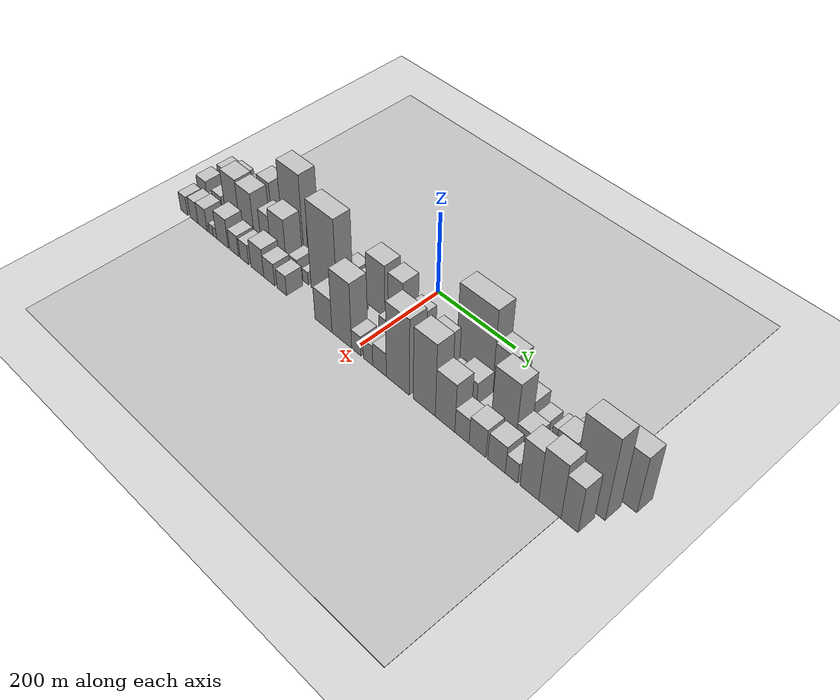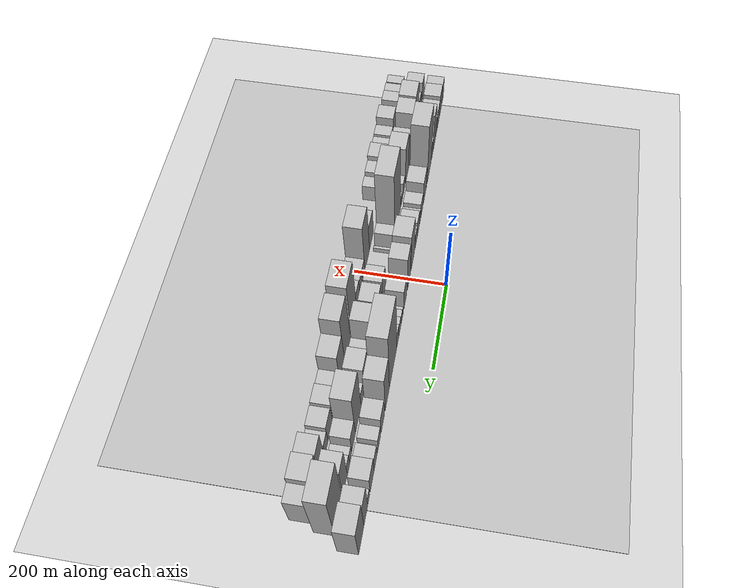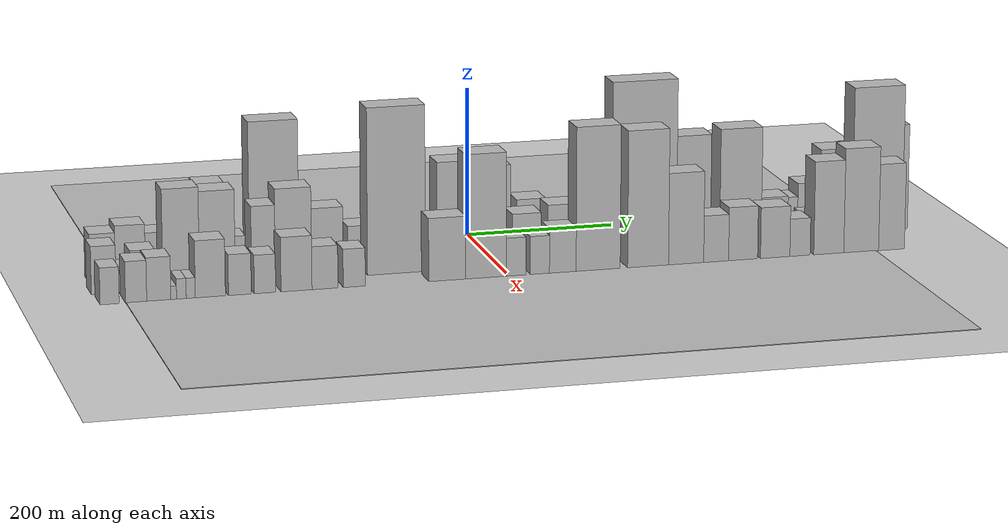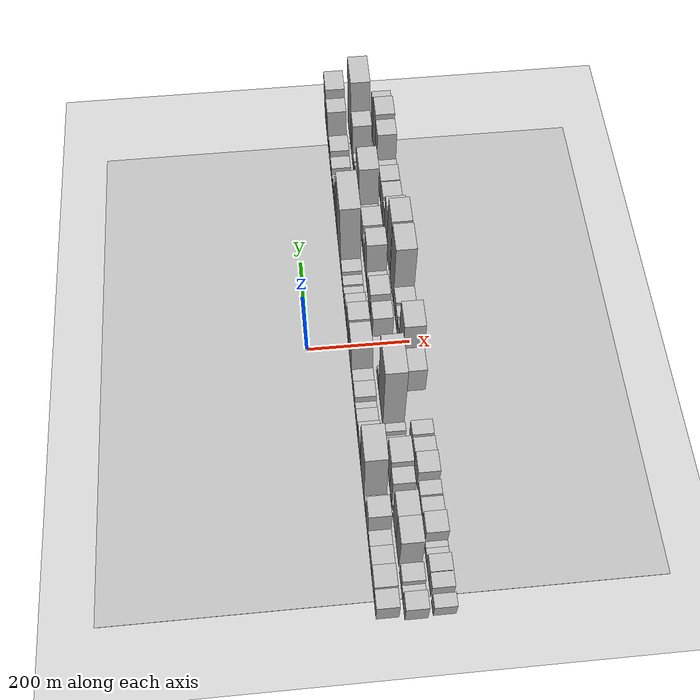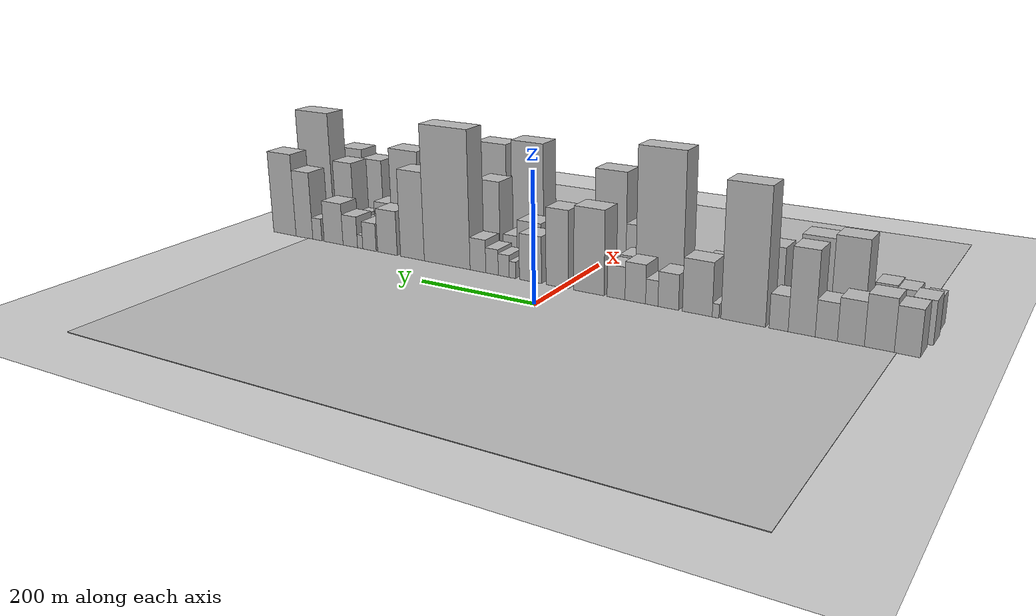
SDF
<?xml version="1.0" encoding="utf-8"?>

<sdf version="1.6">

   <world name="default">

      <gui fullscreen="0">

         <camera name="user_camera">

            <pose>-15 0 4.57585 0 0 0</pose>

            <view_controller>orbit</view_controller>

         </camera>

      </gui>

      <scene>

         <sky>

           <clouds>

             <speed>12</speed>

           </clouds>

         </sky>

         <ambient>0.4 0.4 0.4 1</ambient>

         <background>0.7 0.7 0.7 1</background>

         <shadows>1</shadows>

      </scene>

      <gravity>0 0 -9.8066</gravity>

      <magnetic_field>6e-06 2.3e-05 -4.2e-05</magnetic_field>

      <physics default="0" name="default_physics" type="ode">

         <ode>

            <solver>

               <type>quick</type>

               <iters>10</iters>

               <sor>1.0</sor>

               <use_dynamic_moi_rescaling>0</use_dynamic_moi_rescaling>

            </solver>

            <constraints>

               <cfm>0</cfm>

               <erp>0.2</erp>

               <contact_max_correcting_vel>100</contact_max_correcting_vel>

               <contact_surface_layer>0.001</contact_surface_layer>

            </constraints>

         </ode>

         <max_step_size>0.004</max_step_size>

         <real_time_factor>1</real_time_factor>

         <real_time_update_rate>250</real_time_update_rate>

      </physics>

      <light name="sun" type="directional">

         <cast_shadows>1</cast_shadows>

         <pose>0 0 10 0 0 0</pose>

         <diffuse>0.8 0.8 0.8 1</diffuse>

         <specular>0.2 0.2 0.2 1</specular>

         <attenuation>

            <range>1000</range>

            <constant>0.9</constant>

            <linear>0.01</linear>

            <quadratic>0.001</quadratic>

         </attenuation>

         <direction>-0.5 0.1 -0.9</direction>

      </light>

      <include>

         <name>ground_plane_1</name>

         <uri>model://HANNAS_ground_plane</uri>

         <pose>0 0 0  0 0 0</pose>

      </include>

      <include>

         <name>ground_plane_2</name>

         <uri>model://HANNAS_ground_plane</uri>

         <pose>100 0 0  0 0 0</pose>

      </include>

      <model name="building_1">

         <static>1</static>

         <pose frame="">100.0000 -513.3441 0 0.000000 0.000000 0.000000</pose>

         <link name="link">

            <pose frame="">0 0 33.00 0 0 0</pose>

            <collision name="collision">

               <geometry>

                  <box>

                     <size>40.0000 33.3119 66.0000</size>

                  </box>

               </geometry>

               <max_contacts>10</max_contacts>

               <surface>

                  <contact>

                     <ode/>

                  </contact>

                  <bounce/>

                  <friction>

                     <torsional>

                        <ode/>

                     </torsional>

                     <ode/>

                  </friction>

               </surface>

            </collision>

            <visual name="visual">

               <cast_shadows>0</cast_shadows>

               <geometry>

                  <box>

                     <size>40.0000 33.3119 66.0000</size>

                  </box>

               </geometry>

               <material>

                  <script>

                     <uri>model://HANNAS_wall/materials/scripts</uri>

                     <uri>model://HANNAS_wall/materials/textures</uri>

                     <name>vrc/HANNAS_wall</name>

                  </script>

               </material>

            </visual>

            <self_collide>0</self_collide>

            <enable_wind>0</enable_wind>

            <kinematic>0</kinematic>

         </link>

      </model>

      <model name="building_2">

         <static>1</static>

         <pose frame="">100.0000 -477.1812 0 0.000000 0.000000 0.000000</pose>

         <link name="link">

            <pose frame="">0 0 37.50 0 0 0</pose>

            <collision name="collision">

               <geometry>

                  <box>

                     <size>40.0000 39.0138 75.0000</size>

                  </box>

               </geometry>

               <max_contacts>10</max_contacts>

               <surface>

                  <contact>

                     <ode/>

                  </contact>

                  <bounce/>

                  <friction>

                     <torsional>

                        <ode/>

                     </torsional>

                     <ode/>

                  </friction>

               </surface>

            </collision>

            <visual name="visual">

               <cast_shadows>0</cast_shadows>

               <geometry>

                  <box>

                     <size>40.0000 39.0138 75.0000</size>

                  </box>

               </geometry>

               <material>

                  <script>

                     <uri>model://HANNAS_wall/materials/scripts</uri>

                     <uri>model://HANNAS_wall/materials/textures</uri>

                     <name>vrc/HANNAS_wall</name>

                  </script>

               </material>

            </visual>

            <self_collide>0</self_collide>

            <enable_wind>0</enable_wind>

            <kinematic>0</kinematic>

         </link>

      </model>

      <model name="building_3">

         <static>1</static>

         <pose frame="">100.0000 -439.6910 0 0.000000 0.000000 0.000000</pose>

         <link name="link">

            <pose frame="">0 0 31.50 0 0 0</pose>

            <collision name="collision">

               <geometry>

                  <box>

                     <size>40.0000 35.9666 63.0000</size>

                  </box>

               </geometry>

               <max_contacts>10</max_contacts>

               <surface>

                  <contact>

                     <ode/>

                  </contact>

                  <bounce/>

                  <friction>

                     <torsional>

                        <ode/>

                     </torsional>

                     <ode/>

                  </friction>

               </surface>

            </collision>

            <visual name="visual">

               <cast_shadows>0</cast_shadows>

               <geometry>

                  <box>

                     <size>40.0000 35.9666 63.0000</size>

                  </box>

               </geometry>

               <material>

                  <script>

                     <uri>model://HANNAS_wall/materials/scripts</uri>

                     <uri>model://HANNAS_wall/materials/textures</uri>

                     <name>vrc/HANNAS_wall</name>

                  </script>

               </material>

            </visual>

            <self_collide>0</self_collide>

            <enable_wind>0</enable_wind>

            <kinematic>0</kinematic>

         </link>

      </model>

      <model name="building_4">

         <static>1</static>

         <pose frame="">100.0000 -406.5747 0 0.000000 0.000000 0.000000</pose>

         <link name="link">

            <pose frame="">0 0 27.00 0 0 0</pose>

            <collision name="collision">

               <geometry>

                  <box>

                     <size>40.0000 30.2659 54.0000</size>

                  </box>

               </geometry>

               <max_contacts>10</max_contacts>

               <surface>

                  <contact>

                     <ode/>

                  </contact>

                  <bounce/>

                  <friction>

                     <torsional>

                        <ode/>

                     </torsional>

                     <ode/>

                  </friction>

               </surface>

            </collision>

            <visual name="visual">

               <cast_shadows>0</cast_shadows>

               <geometry>

                  <box>

                     <size>40.0000 30.2659 54.0000</size>

                  </box>

               </geometry>

               <material>

                  <script>

                     <uri>model://HANNAS_wall/materials/scripts</uri>

                     <uri>model://HANNAS_wall/materials/textures</uri>

                     <name>vrc/HANNAS_wall</name>

                  </script>

               </material>

            </visual>

            <self_collide>0</self_collide>

            <enable_wind>0</enable_wind>

            <kinematic>0</kinematic>

         </link>

      </model>

      <model name="building_5">

         <static>1</static>

         <pose frame="">100.0000 -372.5879 0 0.000000 0.000000 0.000000</pose>

         <link name="link">

            <pose frame="">0 0 61.50 0 0 0</pose>

            <collision name="collision">

               <geometry>

                  <box>

                     <size>40.0000 37.7079 123.0000</size>

                  </box>

               </geometry>

               <max_contacts>10</max_contacts>

               <surface>

                  <contact>

                     <ode/>

                  </contact>

                  <bounce/>

                  <friction>

                     <torsional>

                        <ode/>

                     </torsional>

                     <ode/>

                  </friction>

               </surface>

            </collision>

            <visual name="visual">

               <cast_shadows>0</cast_shadows>

               <geometry>

                  <box>

                     <size>40.0000 37.7079 123.0000</size>

                  </box>

               </geometry>

               <material>

                  <script>

                     <uri>model://HANNAS_wall/materials/scripts</uri>

                     <uri>model://HANNAS_wall/materials/textures</uri>

                     <name>vrc/HANNAS_wall</name>

                  </script>

               </material>

            </visual>

            <self_collide>0</self_collide>

            <enable_wind>0</enable_wind>

            <kinematic>0</kinematic>

         </link>

      </model>

      <model name="building_6">

         <static>1</static>

         <pose frame="">100.0000 -340.1390 0 0.000000 0.000000 0.000000</pose>

         <link name="link">

            <pose frame="">0 0 25.50 0 0 0</pose>

            <collision name="collision">

               <geometry>

                  <box>

                     <size>40.0000 27.1898 51.0000</size>

                  </box>

               </geometry>

               <max_contacts>10</max_contacts>

               <surface>

                  <contact>

                     <ode/>

                  </contact>

                  <bounce/>

                  <friction>

                     <torsional>

                        <ode/>

                     </torsional>

                     <ode/>

                  </friction>

               </surface>

            </collision>

            <visual name="visual">

               <cast_shadows>0</cast_shadows>

               <geometry>

                  <box>

                     <size>40.0000 27.1898 51.0000</size>

                  </box>

               </geometry>

               <material>

                  <script>

                     <uri>model://HANNAS_wall/materials/scripts</uri>

                     <uri>model://HANNAS_wall/materials/textures</uri>

                     <name>vrc/HANNAS_wall</name>

                  </script>

               </material>

            </visual>

            <self_collide>0</self_collide>

            <enable_wind>0</enable_wind>

            <kinematic>0</kinematic>

         </link>

      </model>

      <model name="building_7">

         <static>1</static>

         <pose frame="">100.0000 -288.8997 0 0.000000 0.000000 0.000000</pose>

         <link name="link">

            <pose frame="">0 0 100.50 0 0 0</pose>

            <collision name="collision">

               <geometry>

                  <box>

                     <size>40.0000 65.2887 201.0000</size>

                  </box>

               </geometry>

               <max_contacts>10</max_contacts>

               <surface>

                  <contact>

                     <ode/>

                  </contact>

                  <bounce/>

                  <friction>

                     <torsional>

                        <ode/>

                     </torsional>

                     <ode/>

                  </friction>

               </surface>

            </collision>

            <visual name="visual">

               <cast_shadows>0</cast_shadows>

               <geometry>

                  <box>

                     <size>40.0000 65.2887 201.0000</size>

                  </box>

               </geometry>

               <material>

                  <script>

                     <uri>model://HANNAS_wall/materials/scripts</uri>

                     <uri>model://HANNAS_wall/materials/textures</uri>

                     <name>vrc/HANNAS_wall</name>

                  </script>

               </material>

            </visual>

            <self_collide>0</self_collide>

            <enable_wind>0</enable_wind>

            <kinematic>0</kinematic>

         </link>

      </model>

      <model name="building_8">

         <static>1</static>

         <pose frame="">100.0000 -248.1924 0 0.000000 0.000000 0.000000</pose>

         <link name="link">

            <pose frame="">0 0 10.50 0 0 0</pose>

            <collision name="collision">

               <geometry>

                  <box>

                     <size>40.0000 10.1259 21.0000</size>

                  </box>

               </geometry>

               <max_contacts>10</max_contacts>

               <surface>

                  <contact>

                     <ode/>

                  </contact>

                  <bounce/>

                  <friction>

                     <torsional>

                        <ode/>

                     </torsional>

                     <ode/>

                  </friction>

               </surface>

            </collision>

            <visual name="visual">

               <cast_shadows>0</cast_shadows>

               <geometry>

                  <box>

                     <size>40.0000 10.1259 21.0000</size>

                  </box>

               </geometry>

               <material>

                  <script>

                     <uri>model://HANNAS_wall/materials/scripts</uri>

                     <uri>model://HANNAS_wall/materials/textures</uri>

                     <name>vrc/HANNAS_wall</name>

                  </script>

               </material>

            </visual>

            <self_collide>0</self_collide>

            <enable_wind>0</enable_wind>

            <kinematic>0</kinematic>

         </link>

      </model>

      <model name="building_9">

         <static>1</static>

         <pose frame="">100.0000 -220.3343 0 0.000000 0.000000 0.000000</pose>

         <link name="link">

            <pose frame="">0 0 40.50 0 0 0</pose>

            <collision name="collision">

               <geometry>

                  <box>

                     <size>40.0000 45.5904 81.0000</size>

                  </box>

               </geometry>

               <max_contacts>10</max_contacts>

               <surface>

                  <contact>

                     <ode/>

                  </contact>

                  <bounce/>

                  <friction>

                     <torsional>

                        <ode/>

                     </torsional>

                     <ode/>

                  </friction>

               </surface>

            </collision>

            <visual name="visual">

               <cast_shadows>0</cast_shadows>

               <geometry>

                  <box>

                     <size>40.0000 45.5904 81.0000</size>

                  </box>

               </geometry>

               <material>

                  <script>

                     <uri>model://HANNAS_wall/materials/scripts</uri>

                     <uri>model://HANNAS_wall/materials/textures</uri>

                     <name>vrc/HANNAS_wall</name>

                  </script>

               </material>

            </visual>

            <self_collide>0</self_collide>

            <enable_wind>0</enable_wind>

            <kinematic>0</kinematic>

         </link>

      </model>

      <model name="building_10">

         <static>1</static>

         <pose frame="">100.0000 -175.4471 0 0.000000 0.000000 0.000000</pose>

         <link name="link">

            <pose frame="">0 0 27.00 0 0 0</pose>

            <collision name="collision">

               <geometry>

                  <box>

                     <size>40.0000 32.1840 54.0000</size>

                  </box>

               </geometry>

               <max_contacts>10</max_contacts>

               <surface>

                  <contact>

                     <ode/>

                  </contact>

                  <bounce/>

                  <friction>

                     <torsional>

                        <ode/>

                     </torsional>

                     <ode/>

                  </friction>

               </surface>

            </collision>

            <visual name="visual">

               <cast_shadows>0</cast_shadows>

               <geometry>

                  <box>

                     <size>40.0000 32.1840 54.0000</size>

                  </box>

               </geometry>

               <material>

                  <script>

                     <uri>model://HANNAS_wall/materials/scripts</uri>

                     <uri>model://HANNAS_wall/materials/textures</uri>

                     <name>vrc/HANNAS_wall</name>

                  </script>

               </material>

            </visual>

            <self_collide>0</self_collide>

            <enable_wind>0</enable_wind>

            <kinematic>0</kinematic>

         </link>

      </model>

      <model name="building_11">

         <static>1</static>

         <pose frame="">100.0000 -149.4975 0 0.000000 0.000000 0.000000</pose>

         <link name="link">

            <pose frame="">0 0 19.50 0 0 0</pose>

            <collision name="collision">

               <geometry>

                  <box>

                     <size>40.0000 19.7152 39.0000</size>

                  </box>

               </geometry>

               <max_contacts>10</max_contacts>

               <surface>

                  <contact>

                     <ode/>

                  </contact>

                  <bounce/>

                  <friction>

                     <torsional>

                        <ode/>

                     </torsional>

                     <ode/>

                  </friction>

               </surface>

            </collision>

            <visual name="visual">

               <cast_shadows>0</cast_shadows>

               <geometry>

                  <box>

                     <size>40.0000 19.7152 39.0000</size>

                  </box>

               </geometry>

               <material>

                  <script>

                     <uri>model://HANNAS_wall/materials/scripts</uri>

                     <uri>model://HANNAS_wall/materials/textures</uri>

                     <name>vrc/HANNAS_wall</name>

                  </script>

               </material>

            </visual>

            <self_collide>0</self_collide>

            <enable_wind>0</enable_wind>

            <kinematic>0</kinematic>

         </link>

      </model>

      <model name="building_12">

         <static>1</static>

         <pose frame="">100.0000 -122.9814 0 0.000000 0.000000 0.000000</pose>

         <link name="link">

            <pose frame="">0 0 30.00 0 0 0</pose>

            <collision name="collision">

               <geometry>

                  <box>

                     <size>40.0000 33.3170 60.0000</size>

                  </box>

               </geometry>

               <max_contacts>10</max_contacts>

               <surface>

                  <contact>

                     <ode/>

                  </contact>

                  <bounce/>

                  <friction>

                     <torsional>

                        <ode/>

                     </torsional>

                     <ode/>

                  </friction>

               </surface>

            </collision>

            <visual name="visual">

               <cast_shadows>0</cast_shadows>

               <geometry>

                  <box>

                     <size>40.0000 33.3170 60.0000</size>

                  </box>

               </geometry>

               <material>

                  <script>

                     <uri>model://HANNAS_wall/materials/scripts</uri>

                     <uri>model://HANNAS_wall/materials/textures</uri>

                     <name>vrc/HANNAS_wall</name>

                  </script>

               </material>

            </visual>

            <self_collide>0</self_collide>

            <enable_wind>0</enable_wind>

            <kinematic>0</kinematic>

         </link>

      </model>

      <model name="building_13">

         <static>1</static>

         <pose frame="">100.0000 -91.6072 0 0.000000 0.000000 0.000000</pose>

         <link name="link">

            <pose frame="">0 0 25.50 0 0 0</pose>

            <collision name="collision">

               <geometry>

                  <box>

                     <size>40.0000 29.4314 51.0000</size>

                  </box>

               </geometry>

               <max_contacts>10</max_contacts>

               <surface>

                  <contact>

                     <ode/>

                  </contact>

                  <bounce/>

                  <friction>

                     <torsional>

                        <ode/>

                     </torsional>

                     <ode/>

                  </friction>

               </surface>

            </collision>

            <visual name="visual">

               <cast_shadows>0</cast_shadows>

               <geometry>

                  <box>

                     <size>40.0000 29.4314 51.0000</size>

                  </box>

               </geometry>

               <material>

                  <script>

                     <uri>model://HANNAS_wall/materials/scripts</uri>

                     <uri>model://HANNAS_wall/materials/textures</uri>

                     <name>vrc/HANNAS_wall</name>

                  </script>

               </material>

            </visual>

            <self_collide>0</self_collide>

            <enable_wind>0</enable_wind>

            <kinematic>0</kinematic>

         </link>

      </model>

      <model name="building_14">

         <static>1</static>

         <pose frame="">100.0000 -46.2894 0 0.000000 0.000000 0.000000</pose>

         <link name="link">

            <pose frame="">0 0 66.00 0 0 0</pose>

            <collision name="collision">

               <geometry>

                  <box>

                     <size>40.0000 51.2043 132.0000</size>

                  </box>

               </geometry>

               <max_contacts>10</max_contacts>

               <surface>

                  <contact>

                     <ode/>

                  </contact>

                  <bounce/>

                  <friction>

                     <torsional>

                        <ode/>

                     </torsional>

                     <ode/>

                  </friction>

               </surface>

            </collision>

            <visual name="visual">

               <cast_shadows>0</cast_shadows>

               <geometry>

                  <box>

                     <size>40.0000 51.2043 132.0000</size>

                  </box>

               </geometry>

               <material>

                  <script>

                     <uri>model://HANNAS_wall/materials/scripts</uri>

                     <uri>model://HANNAS_wall/materials/textures</uri>

                     <name>vrc/HANNAS_wall</name>

                  </script>

               </material>

            </visual>

            <self_collide>0</self_collide>

            <enable_wind>0</enable_wind>

            <kinematic>0</kinematic>

         </link>

      </model>

      <model name="building_15">

         <static>1</static>

         <pose frame="">100.0000 7.9234 0 0.000000 0.000000 0.000000</pose>

         <link name="link">

            <pose frame="">0 0 61.50 0 0 0</pose>

            <collision name="collision">

               <geometry>

                  <box>

                     <size>40.0000 39.2212 123.0000</size>

                  </box>

               </geometry>

               <max_contacts>10</max_contacts>

               <surface>

                  <contact>

                     <ode/>

                  </contact>

                  <bounce/>

                  <friction>

                     <torsional>

                        <ode/>

                     </torsional>

                     <ode/>

                  </friction>

               </surface>

            </collision>

            <visual name="visual">

               <cast_shadows>0</cast_shadows>

               <geometry>

                  <box>

                     <size>40.0000 39.2212 123.0000</size>

                  </box>

               </geometry>

               <material>

                  <script>

                     <uri>model://HANNAS_wall/materials/scripts</uri>

                     <uri>model://HANNAS_wall/materials/textures</uri>

                     <name>vrc/HANNAS_wall</name>

                  </script>

               </material>

            </visual>

            <self_collide>0</self_collide>

            <enable_wind>0</enable_wind>

            <kinematic>0</kinematic>

         </link>

      </model>

      <model name="building_16">

         <static>1</static>

         <pose frame="">100.0000 55.2420 0 0.000000 0.000000 0.000000</pose>

         <link name="link">

            <pose frame="">0 0 37.50 0 0 0</pose>

            <collision name="collision">

               <geometry>

                  <box>

                     <size>40.0000 39.4160 75.0000</size>

                  </box>

               </geometry>

               <max_contacts>10</max_contacts>

               <surface>

                  <contact>

                     <ode/>

                  </contact>

                  <bounce/>

                  <friction>

                     <torsional>

                        <ode/>

                     </torsional>

                     <ode/>

                  </friction>

               </surface>

            </collision>

            <visual name="visual">

               <cast_shadows>0</cast_shadows>

               <geometry>

                  <box>

                     <size>40.0000 39.4160 75.0000</size>

                  </box>

               </geometry>

               <material>

                  <script>

                     <uri>model://HANNAS_wall/materials/scripts</uri>

                     <uri>model://HANNAS_wall/materials/textures</uri>

                     <name>vrc/HANNAS_wall</name>

                  </script>

               </material>

            </visual>

            <self_collide>0</self_collide>

            <enable_wind>0</enable_wind>

            <kinematic>0</kinematic>

         </link>

      </model>

      <model name="building_17">

         <static>1</static>

         <pose frame="">100.0000 87.6871 0 0.000000 0.000000 0.000000</pose>

         <link name="link">

            <pose frame="">0 0 13.50 0 0 0</pose>

            <collision name="collision">

               <geometry>

                  <box>

                     <size>40.0000 11.4742 27.0000</size>

                  </box>

               </geometry>

               <max_contacts>10</max_contacts>

               <surface>

                  <contact>

                     <ode/>

                  </contact>

                  <bounce/>

                  <friction>

                     <torsional>

                        <ode/>

                     </torsional>

                     <ode/>

                  </friction>

               </surface>

            </collision>

            <visual name="visual">

               <cast_shadows>0</cast_shadows>

               <geometry>

                  <box>

                     <size>40.0000 11.4742 27.0000</size>

                  </box>

               </geometry>

               <material>

                  <script>

                     <uri>model://HANNAS_wall/materials/scripts</uri>

                     <uri>model://HANNAS_wall/materials/textures</uri>

                     <name>vrc/HANNAS_wall</name>

                  </script>

               </material>

            </visual>

            <self_collide>0</self_collide>

            <enable_wind>0</enable_wind>

            <kinematic>0</kinematic>

         </link>

      </model>

      <model name="building_18">

         <static>1</static>

         <pose frame="">100.0000 103.5341 0 0.000000 0.000000 0.000000</pose>

         <link name="link">

            <pose frame="">0 0 18.00 0 0 0</pose>

            <collision name="collision">

               <geometry>

                  <box>

                     <size>40.0000 20.2200 36.0000</size>

                  </box>

               </geometry>

               <max_contacts>10</max_contacts>

               <surface>

                  <contact>

                     <ode/>

                  </contact>

                  <bounce/>

                  <friction>

                     <torsional>

                        <ode/>

                     </torsional>

                     <ode/>

                  </friction>

               </surface>

            </collision>

            <visual name="visual">

               <cast_shadows>0</cast_shadows>

               <geometry>

                  <box>

                     <size>40.0000 20.2200 36.0000</size>

                  </box>

               </geometry>

               <material>

                  <script>

                     <uri>model://HANNAS_wall/materials/scripts</uri>

                     <uri>model://HANNAS_wall/materials/textures</uri>

                     <name>vrc/HANNAS_wall</name>

                  </script>

               </material>

            </visual>

            <self_collide>0</self_collide>

            <enable_wind>0</enable_wind>

            <kinematic>0</kinematic>

         </link>

      </model>

      <model name="building_19">

         <static>1</static>

         <pose frame="">100.0000 125.2188 0 0.000000 0.000000 0.000000</pose>

         <link name="link">

            <pose frame="">0 0 21.00 0 0 0</pose>

            <collision name="collision">

               <geometry>

                  <box>

                     <size>40.0000 23.1493 42.0000</size>

                  </box>

               </geometry>

               <max_contacts>10</max_contacts>

               <surface>

                  <contact>

                     <ode/>

                  </contact>

                  <bounce/>

                  <friction>

                     <torsional>

                        <ode/>

                     </torsional>

                     <ode/>

                  </friction>

               </surface>

            </collision>

            <visual name="visual">

               <cast_shadows>0</cast_shadows>

               <geometry>

                  <box>

                     <size>40.0000 23.1493 42.0000</size>

                  </box>

               </geometry>

               <material>

                  <script>

                     <uri>model://HANNAS_wall/materials/scripts</uri>

                     <uri>model://HANNAS_wall/materials/textures</uri>

                     <name>vrc/HANNAS_wall</name>

                  </script>

               </material>

            </visual>

            <self_collide>0</self_collide>

            <enable_wind>0</enable_wind>

            <kinematic>0</kinematic>

         </link>

      </model>

      <model name="building_20">

         <static>1</static>

         <pose frame="">100.0000 151.5495 0 0.000000 0.000000 0.000000</pose>

         <link name="link">

            <pose frame="">0 0 27.00 0 0 0</pose>

            <collision name="collision">

               <geometry>

                  <box>

                     <size>40.0000 29.5121 54.0000</size>

                  </box>

               </geometry>

               <max_contacts>10</max_contacts>

               <surface>

                  <contact>

                     <ode/>

                  </contact>

                  <bounce/>

                  <friction>

                     <torsional>

                        <ode/>

                     </torsional>

                     <ode/>

                  </friction>

               </surface>

            </collision>

            <visual name="visual">

               <cast_shadows>0</cast_shadows>

               <geometry>

                  <box>

                     <size>40.0000 29.5121 54.0000</size>

                  </box>

               </geometry>

               <material>

                  <script>

                     <uri>model://HANNAS_wall/materials/scripts</uri>

                     <uri>model://HANNAS_wall/materials/textures</uri>

                     <name>vrc/HANNAS_wall</name>

                  </script>

               </material>

            </visual>

            <self_collide>0</self_collide>

            <enable_wind>0</enable_wind>

            <kinematic>0</kinematic>

         </link>

      </model>

      <model name="building_21">

         <static>1</static>

         <pose frame="">100.0000 210.8032 0 0.000000 0.000000 0.000000</pose>

         <link name="link">

            <pose frame="">0 0 112.50 0 0 0</pose>

            <collision name="collision">

               <geometry>

                  <box>

                     <size>40.0000 88.9954 225.0000</size>

                  </box>

               </geometry>

               <max_contacts>10</max_contacts>

               <surface>

                  <contact>

                     <ode/>

                  </contact>

                  <bounce/>

                  <friction>

                     <torsional>

                        <ode/>

                     </torsional>

                     <ode/>

                  </friction>

               </surface>

            </collision>

            <visual name="visual">

               <cast_shadows>0</cast_shadows>

               <geometry>

                  <box>

                     <size>40.0000 88.9954 225.0000</size>

                  </box>

               </geometry>

               <material>

                  <script>

                     <uri>model://HANNAS_wall/materials/scripts</uri>

                     <uri>model://HANNAS_wall/materials/textures</uri>

                     <name>vrc/HANNAS_wall</name>

                  </script>

               </material>

            </visual>

            <self_collide>0</self_collide>

            <enable_wind>0</enable_wind>

            <kinematic>0</kinematic>

         </link>

      </model>

      <model name="building_22">

         <static>1</static>

         <pose frame="">100.0000 279.1438 0 0.000000 0.000000 0.000000</pose>

         <link name="link">

            <pose frame="">0 0 73.50 0 0 0</pose>

            <collision name="collision">

               <geometry>

                  <box>

                     <size>40.0000 47.6858 147.0000</size>

                  </box>

               </geometry>

               <max_contacts>10</max_contacts>

               <surface>

                  <contact>

                     <ode/>

                  </contact>

                  <bounce/>

                  <friction>

                     <torsional>

                        <ode/>

                     </torsional>

                     <ode/>

                  </friction>

               </surface>

            </collision>

            <visual name="visual">

               <cast_shadows>0</cast_shadows>

               <geometry>

                  <box>

                     <size>40.0000 47.6858 147.0000</size>

                  </box>

               </geometry>

               <material>

                  <script>

                     <uri>model://HANNAS_wall/materials/scripts</uri>

                     <uri>model://HANNAS_wall/materials/textures</uri>

                     <name>vrc/HANNAS_wall</name>

                  </script>

               </material>

            </visual>

            <self_collide>0</self_collide>

            <enable_wind>0</enable_wind>

            <kinematic>0</kinematic>

         </link>

      </model>

      <model name="building_23">

         <static>1</static>

         <pose frame="">100.0000 330.2353 0 0.000000 0.000000 0.000000</pose>

         <link name="link">

            <pose frame="">0 0 37.50 0 0 0</pose>

            <collision name="collision">

               <geometry>

                  <box>

                     <size>40.0000 40.4971 75.0000</size>

                  </box>

               </geometry>

               <max_contacts>10</max_contacts>

               <surface>

                  <contact>

                     <ode/>

                  </contact>

                  <bounce/>

                  <friction>

                     <torsional>

                        <ode/>

                     </torsional>

                     <ode/>

                  </friction>

               </surface>

            </collision>

            <visual name="visual">

               <cast_shadows>0</cast_shadows>

               <geometry>

                  <box>

                     <size>40.0000 40.4971 75.0000</size>

                  </box>

               </geometry>

               <material>

                  <script>

                     <uri>model://HANNAS_wall/materials/scripts</uri>

                     <uri>model://HANNAS_wall/materials/textures</uri>

                     <name>vrc/HANNAS_wall</name>

                  </script>

               </material>

            </visual>

            <self_collide>0</self_collide>

            <enable_wind>0</enable_wind>

            <kinematic>0</kinematic>

         </link>

      </model>

      <model name="building_24">

         <static>1</static>

         <pose frame="">100.0000 367.5910 0 0.000000 0.000000 0.000000</pose>

         <link name="link">

            <pose frame="">0 0 24.00 0 0 0</pose>

            <collision name="collision">

               <geometry>

                  <box>

                     <size>40.0000 28.2144 48.0000</size>

                  </box>

               </geometry>

               <max_contacts>10</max_contacts>

               <surface>

                  <contact>

                     <ode/>

                  </contact>

                  <bounce/>

                  <friction>

                     <torsional>

                        <ode/>

                     </torsional>

                     <ode/>

                  </friction>

               </surface>

            </collision>

            <visual name="visual">

               <cast_shadows>0</cast_shadows>

               <geometry>

                  <box>

                     <size>40.0000 28.2144 48.0000</size>

                  </box>

               </geometry>

               <material>

                  <script>

                     <uri>model://HANNAS_wall/materials/scripts</uri>

                     <uri>model://HANNAS_wall/materials/textures</uri>

                     <name>vrc/HANNAS_wall</name>

                  </script>

               </material>

            </visual>

            <self_collide>0</self_collide>

            <enable_wind>0</enable_wind>

            <kinematic>0</kinematic>

         </link>

      </model>

      <model name="building_25">

         <static>1</static>

         <pose frame="">100.0000 387.3323 0 0.000000 0.000000 0.000000</pose>

         <link name="link">

            <pose frame="">0 0 12.00 0 0 0</pose>

            <collision name="collision">

               <geometry>

                  <box>

                     <size>40.0000 11.2683 24.0000</size>

                  </box>

               </geometry>

               <max_contacts>10</max_contacts>

               <surface>

                  <contact>

                     <ode/>

                  </contact>

                  <bounce/>

                  <friction>

                     <torsional>

                        <ode/>

                     </torsional>

                     <ode/>

                  </friction>

               </surface>

            </collision>

            <visual name="visual">

               <cast_shadows>0</cast_shadows>

               <geometry>

                  <box>

                     <size>40.0000 11.2683 24.0000</size>

                  </box>

               </geometry>

               <material>

                  <script>

                     <uri>model://HANNAS_wall/materials/scripts</uri>

                     <uri>model://HANNAS_wall/materials/textures</uri>

                     <name>vrc/HANNAS_wall</name>

                  </script>

               </material>

            </visual>

            <self_collide>0</self_collide>

            <enable_wind>0</enable_wind>

            <kinematic>0</kinematic>

         </link>

      </model>

      <model name="building_26">

         <static>1</static>

         <pose frame="">100.0000 408.5365 0 0.000000 0.000000 0.000000</pose>

         <link name="link">

            <pose frame="">0 0 27.00 0 0 0</pose>

            <collision name="collision">

               <geometry>

                  <box>

                     <size>40.0000 31.1400 54.0000</size>

                  </box>

               </geometry>

               <max_contacts>10</max_contacts>

               <surface>

                  <contact>

                     <ode/>

                  </contact>

                  <bounce/>

                  <friction>

                     <torsional>

                        <ode/>

                     </torsional>

                     <ode/>

                  </friction>

               </surface>

            </collision>

            <visual name="visual">

               <cast_shadows>0</cast_shadows>

               <geometry>

                  <box>

                     <size>40.0000 31.1400 54.0000</size>

                  </box>

               </geometry>

               <material>

                  <script>

                     <uri>model://HANNAS_wall/materials/scripts</uri>

                     <uri>model://HANNAS_wall/materials/textures</uri>

                     <name>vrc/HANNAS_wall</name>

                  </script>

               </material>

            </visual>

            <self_collide>0</self_collide>

            <enable_wind>0</enable_wind>

            <kinematic>0</kinematic>

         </link>

      </model>

      <model name="building_27">

         <static>1</static>

         <pose frame="">100.0000 444.8234 0 0.000000 0.000000 0.000000</pose>

         <link name="link">

            <pose frame="">0 0 36.00 0 0 0</pose>

            <collision name="collision">

               <geometry>

                  <box>

                     <size>40.0000 41.4338 72.0000</size>

                  </box>

               </geometry>

               <max_contacts>10</max_contacts>

               <surface>

                  <contact>

                     <ode/>

                  </contact>

                  <bounce/>

                  <friction>

                     <torsional>

                        <ode/>

                     </torsional>

                     <ode/>

                  </friction>

               </surface>

            </collision>

            <visual name="visual">

               <cast_shadows>0</cast_shadows>

               <geometry>

                  <box>

                     <size>40.0000 41.4338 72.0000</size>

                  </box>

               </geometry>

               <material>

                  <script>

                     <uri>model://HANNAS_wall/materials/scripts</uri>

                     <uri>model://HANNAS_wall/materials/textures</uri>

                     <name>vrc/HANNAS_wall</name>

                  </script>

               </material>

            </visual>

            <self_collide>0</self_collide>

            <enable_wind>0</enable_wind>

            <kinematic>0</kinematic>

         </link>

      </model>

      <model name="building_28">

         <static>1</static>

         <pose frame="">100.0000 480.5963 0 0.000000 0.000000 0.000000</pose>

         <link name="link">

            <pose frame="">0 0 19.50 0 0 0</pose>

            <collision name="collision">

               <geometry>

                  <box>

                     <size>40.0000 20.1121 39.0000</size>

                  </box>

               </geometry>

               <max_contacts>10</max_contacts>

               <surface>

                  <contact>

                     <ode/>

                  </contact>

                  <bounce/>

                  <friction>

                     <torsional>

                        <ode/>

                     </torsional>

                     <ode/>

                  </friction>

               </surface>

            </collision>

            <visual name="visual">

               <cast_shadows>0</cast_shadows>

               <geometry>

                  <box>

                     <size>40.0000 20.1121 39.0000</size>

                  </box>

               </geometry>

               <material>

                  <script>

                     <uri>model://HANNAS_wall/materials/scripts</uri>

                     <uri>model://HANNAS_wall/materials/textures</uri>

                     <name>vrc/HANNAS_wall</name>

                  </script>

               </material>

            </visual>

            <self_collide>0</self_collide>

            <enable_wind>0</enable_wind>

            <kinematic>0</kinematic>

         </link>

      </model>

      <model name="building_29">

         <static>1</static>

         <pose frame="">100.0000 509.6059 0 0.000000 0.000000 0.000000</pose>

         <link name="link">

            <pose frame="">0 0 58.50 0 0 0</pose>

            <collision name="collision">

               <geometry>

                  <box>

                     <size>40.0000 37.9071 117.0000</size>

                  </box>

               </geometry>

               <max_contacts>10</max_contacts>

               <surface>

                  <contact>

                     <ode/>

                  </contact>

                  <bounce/>

                  <friction>

                     <torsional>

                        <ode/>

                     </torsional>

                     <ode/>

                  </friction>

               </surface>

            </collision>

            <visual name="visual">

               <cast_shadows>0</cast_shadows>

               <geometry>

                  <box>

                     <size>40.0000 37.9071 117.0000</size>

                  </box>

               </geometry>

               <material>

                  <script>

                     <uri>model://HANNAS_wall/materials/scripts</uri>

                     <uri>model://HANNAS_wall/materials/textures</uri>

                     <name>vrc/HANNAS_wall</name>

                  </script>

               </material>

            </visual>

            <self_collide>0</self_collide>

            <enable_wind>0</enable_wind>

            <kinematic>0</kinematic>

         </link>

      </model>

      <model name="building_30">

         <static>1</static>

         <pose frame="">100.0000 554.2953 0 0.000000 0.000000 0.000000</pose>

         <link name="link">

            <pose frame="">0 0 72.00 0 0 0</pose>

            <collision name="collision">

               <geometry>

                  <box>

                     <size>40.0000 51.4716 144.0000</size>

                  </box>

               </geometry>

               <max_contacts>10</max_contacts>

               <surface>

                  <contact>

                     <ode/>

                  </contact>

                  <bounce/>

                  <friction>

                     <torsional>

                        <ode/>

                     </torsional>

                     <ode/>

                  </friction>

               </surface>

            </collision>

            <visual name="visual">

               <cast_shadows>0</cast_shadows>

               <geometry>

                  <box>

                     <size>40.0000 51.4716 144.0000</size>

                  </box>

               </geometry>

               <material>

                  <script>

                     <uri>model://HANNAS_wall/materials/scripts</uri>

                     <uri>model://HANNAS_wall/materials/textures</uri>

                     <name>vrc/HANNAS_wall</name>

                  </script>

               </material>

            </visual>

            <self_collide>0</self_collide>

            <enable_wind>0</enable_wind>

            <kinematic>0</kinematic>

         </link>

      </model>

      <model name="building_31">

         <static>1</static>

         <pose frame="">149.0000 -520.1009 0 0.000000 0.000000 0.000000</pose>

         <link name="link">

            <pose frame="">0 0 31.50 0 0 0</pose>

            <collision name="collision">

               <geometry>

                  <box>

                     <size>40.0000 31.7982 63.0000</size>

                  </box>

               </geometry>

               <max_contacts>10</max_contacts>

               <surface>

                  <contact>

                     <ode/>

                  </contact>

                  <bounce/>

                  <friction>

                     <torsional>

                        <ode/>

                     </torsional>

                     <ode/>

                  </friction>

               </surface>

            </collision>

            <visual name="visual">

               <cast_shadows>0</cast_shadows>

               <geometry>

                  <box>

                     <size>40.0000 31.7982 63.0000</size>

                  </box>

               </geometry>

               <material>

                  <script>

                     <uri>model://HANNAS_wall/materials/scripts</uri>

                     <uri>model://HANNAS_wall/materials/textures</uri>

                     <name>vrc/HANNAS_wall</name>

                  </script>

               </material>

            </visual>

            <self_collide>0</self_collide>

            <enable_wind>0</enable_wind>

            <kinematic>0</kinematic>

         </link>

      </model>

      <model name="building_32">

         <static>1</static>

         <pose frame="">149.0000 -494.9690 0 0.000000 0.000000 0.000000</pose>

         <link name="link">

            <pose frame="">0 0 16.50 0 0 0</pose>

            <collision name="collision">

               <geometry>

                  <box>

                     <size>40.0000 18.4654 33.0000</size>

                  </box>

               </geometry>

               <max_contacts>10</max_contacts>

               <surface>

                  <contact>

                     <ode/>

                  </contact>

                  <bounce/>

                  <friction>

                     <torsional>

                        <ode/>

                     </torsional>

                     <ode/>

                  </friction>

               </surface>

            </collision>

            <visual name="visual">

               <cast_shadows>0</cast_shadows>

               <geometry>

                  <box>

                     <size>40.0000 18.4654 33.0000</size>

                  </box>

               </geometry>

               <material>

                  <script>

                     <uri>model://HANNAS_wall/materials/scripts</uri>

                     <uri>model://HANNAS_wall/materials/textures</uri>

                     <name>vrc/HANNAS_wall</name>

                  </script>

               </material>

            </visual>

            <self_collide>0</self_collide>

            <enable_wind>0</enable_wind>

            <kinematic>0</kinematic>

         </link>

      </model>

      <model name="building_33">

         <static>1</static>

         <pose frame="">149.0000 -469.7545 0 0.000000 0.000000 0.000000</pose>

         <link name="link">

            <pose frame="">0 0 27.00 0 0 0</pose>

            <collision name="collision">

               <geometry>

                  <box>

                     <size>40.0000 31.9637 54.0000</size>

                  </box>

               </geometry>

               <max_contacts>10</max_contacts>

               <surface>

                  <contact>

                     <ode/>

                  </contact>

                  <bounce/>

                  <friction>

                     <torsional>

                        <ode/>

                     </torsional>

                     <ode/>

                  </friction>

               </surface>

            </collision>

            <visual name="visual">

               <cast_shadows>0</cast_shadows>

               <geometry>

                  <box>

                     <size>40.0000 31.9637 54.0000</size>

                  </box>

               </geometry>

               <material>

                  <script>

                     <uri>model://HANNAS_wall/materials/scripts</uri>

                     <uri>model://HANNAS_wall/materials/textures</uri>

                     <name>vrc/HANNAS_wall</name>

                  </script>

               </material>

            </visual>

            <self_collide>0</self_collide>

            <enable_wind>0</enable_wind>

            <kinematic>0</kinematic>

         </link>

      </model>

      <model name="building_34">

         <static>1</static>

         <pose frame="">149.0000 -420.1335 0 0.000000 0.000000 0.000000</pose>

         <link name="link">

            <pose frame="">0 0 66.00 0 0 0</pose>

            <collision name="collision">

               <geometry>

                  <box>

                     <size>40.0000 47.2783 132.0000</size>

                  </box>

               </geometry>

               <max_contacts>10</max_contacts>

               <surface>

                  <contact>

                     <ode/>

                  </contact>

                  <bounce/>

                  <friction>

                     <torsional>

                        <ode/>

                     </torsional>

                     <ode/>

                  </friction>

               </surface>

            </collision>

            <visual name="visual">

               <cast_shadows>0</cast_shadows>

               <geometry>

                  <box>

                     <size>40.0000 47.2783 132.0000</size>

                  </box>

               </geometry>

               <material>

                  <script>

                     <uri>model://HANNAS_wall/materials/scripts</uri>

                     <uri>model://HANNAS_wall/materials/textures</uri>

                     <name>vrc/HANNAS_wall</name>

                  </script>

               </material>

            </visual>

            <self_collide>0</self_collide>

            <enable_wind>0</enable_wind>

            <kinematic>0</kinematic>

         </link>

      </model>

      <model name="building_35">

         <static>1</static>

         <pose frame="">149.0000 -373.2348 0 0.000000 0.000000 0.000000</pose>

         <link name="link">

            <pose frame="">0 0 63.00 0 0 0</pose>

            <collision name="collision">

               <geometry>

                  <box>

                     <size>40.0000 46.5190 126.0000</size>

                  </box>

               </geometry>

               <max_contacts>10</max_contacts>

               <surface>

                  <contact>

                     <ode/>

                  </contact>

                  <bounce/>

                  <friction>

                     <torsional>

                        <ode/>

                     </torsional>

                     <ode/>

                  </friction>

               </surface>

            </collision>

            <visual name="visual">

               <cast_shadows>0</cast_shadows>

               <geometry>

                  <box>

                     <size>40.0000 46.5190 126.0000</size>

                  </box>

               </geometry>

               <material>

                  <script>

                     <uri>model://HANNAS_wall/materials/scripts</uri>

                     <uri>model://HANNAS_wall/materials/textures</uri>

                     <name>vrc/HANNAS_wall</name>

                  </script>

               </material>

            </visual>

            <self_collide>0</self_collide>

            <enable_wind>0</enable_wind>

            <kinematic>0</kinematic>

         </link>

      </model>

      <model name="building_36">

         <static>1</static>

         <pose frame="">149.0000 -334.3465 0 0.000000 0.000000 0.000000</pose>

         <link name="link">

            <pose frame="">0 0 12.00 0 0 0</pose>

            <collision name="collision">

               <geometry>

                  <box>

                     <size>40.0000 11.2576 24.0000</size>

                  </box>

               </geometry>

               <max_contacts>10</max_contacts>

               <surface>

                  <contact>

                     <ode/>

                  </contact>

                  <bounce/>

                  <friction>

                     <torsional>

                        <ode/>

                     </torsional>

                     <ode/>

                  </friction>

               </surface>

            </collision>

            <visual name="visual">

               <cast_shadows>0</cast_shadows>

               <geometry>

                  <box>

                     <size>40.0000 11.2576 24.0000</size>

                  </box>

               </geometry>

               <material>

                  <script>

                     <uri>model://HANNAS_wall/materials/scripts</uri>

                     <uri>model://HANNAS_wall/materials/textures</uri>

                     <name>vrc/HANNAS_wall</name>

                  </script>

               </material>

            </visual>

            <self_collide>0</self_collide>

            <enable_wind>0</enable_wind>

            <kinematic>0</kinematic>

         </link>

      </model>

      <model name="building_37">

         <static>1</static>

         <pose frame="">149.0000 -313.2042 0 0.000000 0.000000 0.000000</pose>

         <link name="link">

            <pose frame="">0 0 51.00 0 0 0</pose>

            <collision name="collision">

               <geometry>

                  <box>

                     <size>40.0000 31.0270 102.0000</size>

                  </box>

               </geometry>

               <max_contacts>10</max_contacts>

               <surface>

                  <contact>

                     <ode/>

                  </contact>

                  <bounce/>

                  <friction>

                     <torsional>

                        <ode/>

                     </torsional>

                     <ode/>

                  </friction>

               </surface>

            </collision>

            <visual name="visual">

               <cast_shadows>0</cast_shadows>

               <geometry>

                  <box>

                     <size>40.0000 31.0270 102.0000</size>

                  </box>

               </geometry>

               <material>

                  <script>

                     <uri>model://HANNAS_wall/materials/scripts</uri>

                     <uri>model://HANNAS_wall/materials/textures</uri>

                     <name>vrc/HANNAS_wall</name>

                  </script>

               </material>

            </visual>

            <self_collide>0</self_collide>

            <enable_wind>0</enable_wind>

            <kinematic>0</kinematic>

         </link>

      </model>

      <model name="building_38">

         <static>1</static>

         <pose frame="">149.0000 -273.9152 0 0.000000 0.000000 0.000000</pose>

         <link name="link">

            <pose frame="">0 0 61.50 0 0 0</pose>

            <collision name="collision">

               <geometry>

                  <box>

                     <size>40.0000 47.5510 123.0000</size>

                  </box>

               </geometry>

               <max_contacts>10</max_contacts>

               <surface>

                  <contact>

                     <ode/>

                  </contact>

                  <bounce/>

                  <friction>

                     <torsional>

                        <ode/>

                     </torsional>

                     <ode/>

                  </friction>

               </surface>

            </collision>

            <visual name="visual">

               <cast_shadows>0</cast_shadows>

               <geometry>

                  <box>

                     <size>40.0000 47.5510 123.0000</size>

                  </box>

               </geometry>

               <material>

                  <script>

                     <uri>model://HANNAS_wall/materials/scripts</uri>

                     <uri>model://HANNAS_wall/materials/textures</uri>

                     <name>vrc/HANNAS_wall</name>

                  </script>

               </material>

            </visual>

            <self_collide>0</self_collide>

            <enable_wind>0</enable_wind>

            <kinematic>0</kinematic>

         </link>

      </model>

      <model name="building_39">

         <static>1</static>

         <pose frame="">149.0000 -229.0265 0 0.000000 0.000000 0.000000</pose>

         <link name="link">

            <pose frame="">0 0 21.00 0 0 0</pose>

            <collision name="collision">

               <geometry>

                  <box>

                     <size>40.0000 24.2266 42.0000</size>

                  </box>

               </geometry>

               <max_contacts>10</max_contacts>

               <surface>

                  <contact>

                     <ode/>

                  </contact>

                  <bounce/>

                  <friction>

                     <torsional>

                        <ode/>

                     </torsional>

                     <ode/>

                  </friction>

               </surface>

            </collision>

            <visual name="visual">

               <cast_shadows>0</cast_shadows>

               <geometry>

                  <box>

                     <size>40.0000 24.2266 42.0000</size>

                  </box>

               </geometry>

               <material>

                  <script>

                     <uri>model://HANNAS_wall/materials/scripts</uri>

                     <uri>model://HANNAS_wall/materials/textures</uri>

                     <name>vrc/HANNAS_wall</name>

                  </script>

               </material>

            </visual>

            <self_collide>0</self_collide>

            <enable_wind>0</enable_wind>

            <kinematic>0</kinematic>

         </link>

      </model>

      <model name="building_40">

         <static>1</static>

         <pose frame="">149.0000 -205.2852 0 0.000000 0.000000 0.000000</pose>

         <link name="link">

            <pose frame="">0 0 7.50 0 0 0</pose>

            <collision name="collision">

               <geometry>

                  <box>

                     <size>40.0000 7.2558 15.0000</size>

                  </box>

               </geometry>

               <max_contacts>10</max_contacts>

               <surface>

                  <contact>

                     <ode/>

                  </contact>

                  <bounce/>

                  <friction>

                     <torsional>

                        <ode/>

                     </torsional>

                     <ode/>

                  </friction>

               </surface>

            </collision>

            <visual name="visual">

               <cast_shadows>0</cast_shadows>

               <geometry>

                  <box>

                     <size>40.0000 7.2558 15.0000</size>

                  </box>

               </geometry>

               <material>

                  <script>

                     <uri>model://HANNAS_wall/materials/scripts</uri>

                     <uri>model://HANNAS_wall/materials/textures</uri>

                     <name>vrc/HANNAS_wall</name>

                  </script>

               </material>

            </visual>

            <self_collide>0</self_collide>

            <enable_wind>0</enable_wind>

            <kinematic>0</kinematic>

         </link>

      </model>

      <model name="building_41">

         <static>1</static>

         <pose frame="">149.0000 -193.0816 0 0.000000 0.000000 0.000000</pose>

         <link name="link">

            <pose frame="">0 0 16.50 0 0 0</pose>

            <collision name="collision">

               <geometry>

                  <box>

                     <size>40.0000 17.1515 33.0000</size>

                  </box>

               </geometry>

               <max_contacts>10</max_contacts>

               <surface>

                  <contact>

                     <ode/>

                  </contact>

                  <bounce/>

                  <friction>

                     <torsional>

                        <ode/>

                     </torsional>

                     <ode/>

                  </friction>

               </surface>

            </collision>

            <visual name="visual">

               <cast_shadows>0</cast_shadows>

               <geometry>

                  <box>

                     <size>40.0000 17.1515 33.0000</size>

                  </box>

               </geometry>

               <material>

                  <script>

                     <uri>model://HANNAS_wall/materials/scripts</uri>

                     <uri>model://HANNAS_wall/materials/textures</uri>

                     <name>vrc/HANNAS_wall</name>

                  </script>

               </material>

            </visual>

            <self_collide>0</self_collide>

            <enable_wind>0</enable_wind>

            <kinematic>0</kinematic>

         </link>

      </model>

      <model name="building_42">

         <static>1</static>

         <pose frame="">149.0000 -138.0762 0 0.000000 0.000000 0.000000</pose>

         <link name="link">

            <pose frame="">0 0 111.00 0 0 0</pose>

            <collision name="collision">

               <geometry>

                  <box>

                     <size>40.0000 76.8591 222.0000</size>

                  </box>

               </geometry>

               <max_contacts>10</max_contacts>

               <surface>

                  <contact>

                     <ode/>

                  </contact>

                  <bounce/>

                  <friction>

                     <torsional>

                        <ode/>

                     </torsional>

                     <ode/>

                  </friction>

               </surface>

            </collision>

            <visual name="visual">

               <cast_shadows>0</cast_shadows>

               <geometry>

                  <box>

                     <size>40.0000 76.8591 222.0000</size>

                  </box>

               </geometry>

               <material>

                  <script>

                     <uri>model://HANNAS_wall/materials/scripts</uri>

                     <uri>model://HANNAS_wall/materials/textures</uri>

                     <name>vrc/HANNAS_wall</name>

                  </script>

               </material>

            </visual>

            <self_collide>0</self_collide>

            <enable_wind>0</enable_wind>

            <kinematic>0</kinematic>

         </link>

      </model>

      <model name="building_43">

         <static>1</static>

         <pose frame="">149.0000 -86.1121 0 0.000000 0.000000 0.000000</pose>

         <link name="link">

            <pose frame="">0 0 25.50 0 0 0</pose>

            <collision name="collision">

               <geometry>

                  <box>

                     <size>40.0000 27.0691 51.0000</size>

                  </box>

               </geometry>

               <max_contacts>10</max_contacts>

               <surface>

                  <contact>

                     <ode/>

                  </contact>

                  <bounce/>

                  <friction>

                     <torsional>

                        <ode/>

                     </torsional>

                     <ode/>

                  </friction>

               </surface>

            </collision>

            <visual name="visual">

               <cast_shadows>0</cast_shadows>

               <geometry>

                  <box>

                     <size>40.0000 27.0691 51.0000</size>

                  </box>

               </geometry>

               <material>

                  <script>

                     <uri>model://HANNAS_wall/materials/scripts</uri>

                     <uri>model://HANNAS_wall/materials/textures</uri>

                     <name>vrc/HANNAS_wall</name>

                  </script>

               </material>

            </visual>

            <self_collide>0</self_collide>

            <enable_wind>0</enable_wind>

            <kinematic>0</kinematic>

         </link>

      </model>

      <model name="building_44">

         <static>1</static>

         <pose frame="">149.0000 -60.4198 0 0.000000 0.000000 0.000000</pose>

         <link name="link">

            <pose frame="">0 0 7.50 0 0 0</pose>

            <collision name="collision">

               <geometry>

                  <box>

                     <size>40.0000 6.3156 15.0000</size>

                  </box>

               </geometry>

               <max_contacts>10</max_contacts>

               <surface>

                  <contact>

                     <ode/>

                  </contact>

                  <bounce/>

                  <friction>

                     <torsional>

                        <ode/>

                     </torsional>

                     <ode/>

                  </friction>

               </surface>

            </collision>

            <visual name="visual">

               <cast_shadows>0</cast_shadows>

               <geometry>

                  <box>

                     <size>40.0000 6.3156 15.0000</size>

                  </box>

               </geometry>

               <material>

                  <script>

                     <uri>model://HANNAS_wall/materials/scripts</uri>

                     <uri>model://HANNAS_wall/materials/textures</uri>

                     <name>vrc/HANNAS_wall</name>

                  </script>

               </material>

            </visual>

            <self_collide>0</self_collide>

            <enable_wind>0</enable_wind>

            <kinematic>0</kinematic>

         </link>

      </model>

      <model name="building_45">

         <static>1</static>

         <pose frame="">149.0000 36.3781 0 0.000000 0.000000 0.000000</pose>

         <link name="link">

            <pose frame="">0 0 34.50 0 0 0</pose>

            <collision name="collision">

               <geometry>

                  <box>

                     <size>40.0000 39.0934 69.0000</size>

                  </box>

               </geometry>

               <max_contacts>10</max_contacts>

               <surface>

                  <contact>

                     <ode/>

                  </contact>

                  <bounce/>

                  <friction>

                     <torsional>

                        <ode/>

                     </torsional>

                     <ode/>

                  </friction>

               </surface>

            </collision>

            <visual name="visual">

               <cast_shadows>0</cast_shadows>

               <geometry>

                  <box>

                     <size>40.0000 39.0934 69.0000</size>

                  </box>

               </geometry>

               <material>

                  <script>

                     <uri>model://HANNAS_wall/materials/scripts</uri>

                     <uri>model://HANNAS_wall/materials/textures</uri>

                     <name>vrc/HANNAS_wall</name>

                  </script>

               </material>

            </visual>

            <self_collide>0</self_collide>

            <enable_wind>0</enable_wind>

            <kinematic>0</kinematic>

         </link>

      </model>

      <model name="building_46">

         <static>1</static>

         <pose frame="">149.0000 87.0052 0 0.000000 0.000000 0.000000</pose>

         <link name="link">

            <pose frame="">0 0 39.00 0 0 0</pose>

            <collision name="collision">

               <geometry>

                  <box>

                     <size>40.0000 44.1608 78.0000</size>

                  </box>

               </geometry>

               <max_contacts>10</max_contacts>

               <surface>

                  <contact>

                     <ode/>

                  </contact>

                  <bounce/>

                  <friction>

                     <torsional>

                        <ode/>

                     </torsional>

                     <ode/>

                  </friction>

               </surface>

            </collision>

            <visual name="visual">

               <cast_shadows>0</cast_shadows>

               <geometry>

                  <box>

                     <size>40.0000 44.1608 78.0000</size>

                  </box>

               </geometry>

               <material>

                  <script>

                     <uri>model://HANNAS_wall/materials/scripts</uri>

                     <uri>model://HANNAS_wall/materials/textures</uri>

                     <name>vrc/HANNAS_wall</name>

                  </script>

               </material>

            </visual>

            <self_collide>0</self_collide>

            <enable_wind>0</enable_wind>

            <kinematic>0</kinematic>

         </link>

      </model>

      <model name="building_47">

         <static>1</static>

         <pose frame="">149.0000 122.1016 0 0.000000 0.000000 0.000000</pose>

         <link name="link">

            <pose frame="">0 0 25.50 0 0 0</pose>

            <collision name="collision">

               <geometry>

                  <box>

                     <size>40.0000 26.0319 51.0000</size>

                  </box>

               </geometry>

               <max_contacts>10</max_contacts>

               <surface>

                  <contact>

                     <ode/>

                  </contact>

                  <bounce/>

                  <friction>

                     <torsional>

                        <ode/>

                     </torsional>

                     <ode/>

                  </friction>

               </surface>

            </collision>

            <visual name="visual">

               <cast_shadows>0</cast_shadows>

               <geometry>

                  <box>

                     <size>40.0000 26.0319 51.0000</size>

                  </box>

               </geometry>

               <material>

                  <script>

                     <uri>model://HANNAS_wall/materials/scripts</uri>

                     <uri>model://HANNAS_wall/materials/textures</uri>

                     <name>vrc/HANNAS_wall</name>

                  </script>

               </material>

            </visual>

            <self_collide>0</self_collide>

            <enable_wind>0</enable_wind>

            <kinematic>0</kinematic>

         </link>

      </model>

      <model name="building_48">

         <static>1</static>

         <pose frame="">149.0000 161.9994 0 0.000000 0.000000 0.000000</pose>

         <link name="link">

            <pose frame="">0 0 67.50 0 0 0</pose>

            <collision name="collision">

               <geometry>

                  <box>

                     <size>40.0000 41.7636 135.0000</size>

                  </box>

               </geometry>

               <max_contacts>10</max_contacts>

               <surface>

                  <contact>

                     <ode/>

                  </contact>

                  <bounce/>

                  <friction>

                     <torsional>

                        <ode/>

                     </torsional>

                     <ode/>

                  </friction>

               </surface>

            </collision>

            <visual name="visual">

               <cast_shadows>0</cast_shadows>

               <geometry>

                  <box>

                     <size>40.0000 41.7636 135.0000</size>

                  </box>

               </geometry>

               <material>

                  <script>

                     <uri>model://HANNAS_wall/materials/scripts</uri>

                     <uri>model://HANNAS_wall/materials/textures</uri>

                     <name>vrc/HANNAS_wall</name>

                  </script>

               </material>

            </visual>

            <self_collide>0</self_collide>

            <enable_wind>0</enable_wind>

            <kinematic>0</kinematic>

         </link>

      </model>

      <model name="building_49">

         <static>1</static>

         <pose frame="">149.0000 201.9454 0 0.000000 0.000000 0.000000</pose>

         <link name="link">

            <pose frame="">0 0 31.50 0 0 0</pose>

            <collision name="collision">

               <geometry>

                  <box>

                     <size>40.0000 32.1285 63.0000</size>

                  </box>

               </geometry>

               <max_contacts>10</max_contacts>

               <surface>

                  <contact>

                     <ode/>

                  </contact>

                  <bounce/>

                  <friction>

                     <torsional>

                        <ode/>

                     </torsional>

                     <ode/>

                  </friction>

               </surface>

            </collision>

            <visual name="visual">

               <cast_shadows>0</cast_shadows>

               <geometry>

                  <box>

                     <size>40.0000 32.1285 63.0000</size>

                  </box>

               </geometry>

               <material>

                  <script>

                     <uri>model://HANNAS_wall/materials/scripts</uri>

                     <uri>model://HANNAS_wall/materials/textures</uri>

                     <name>vrc/HANNAS_wall</name>

                  </script>

               </material>

            </visual>

            <self_collide>0</self_collide>

            <enable_wind>0</enable_wind>

            <kinematic>0</kinematic>

         </link>

      </model>

      <model name="building_50">

         <static>1</static>

         <pose frame="">149.0000 241.2826 0 0.000000 0.000000 0.000000</pose>

         <link name="link">

            <pose frame="">0 0 45.00 0 0 0</pose>

            <collision name="collision">

               <geometry>

                  <box>

                     <size>40.0000 46.5459 90.0000</size>

                  </box>

               </geometry>

               <max_contacts>10</max_contacts>

               <surface>

                  <contact>

                     <ode/>

                  </contact>

                  <bounce/>

                  <friction>

                     <torsional>

                        <ode/>

                     </torsional>

                     <ode/>

                  </friction>

               </surface>

            </collision>

            <visual name="visual">

               <cast_shadows>0</cast_shadows>

               <geometry>

                  <box>

                     <size>40.0000 46.5459 90.0000</size>

                  </box>

               </geometry>

               <material>

                  <script>

                     <uri>model://HANNAS_wall/materials/scripts</uri>

                     <uri>model://HANNAS_wall/materials/textures</uri>

                     <name>vrc/HANNAS_wall</name>

                  </script>

               </material>

            </visual>

            <self_collide>0</self_collide>

            <enable_wind>0</enable_wind>

            <kinematic>0</kinematic>

         </link>

      </model>

      <model name="building_51">

         <static>1</static>

         <pose frame="">149.0000 267.8641 0 0.000000 0.000000 0.000000</pose>

         <link name="link">

            <pose frame="">0 0 7.50 0 0 0</pose>

            <collision name="collision">

               <geometry>

                  <box>

                     <size>40.0000 6.6171 15.0000</size>

                  </box>

               </geometry>

               <max_contacts>10</max_contacts>

               <surface>

                  <contact>

                     <ode/>

                  </contact>

                  <bounce/>

                  <friction>

                     <torsional>

                        <ode/>

                     </torsional>

                     <ode/>

                  </friction>

               </surface>

            </collision>

            <visual name="visual">

               <cast_shadows>0</cast_shadows>

               <geometry>

                  <box>

                     <size>40.0000 6.6171 15.0000</size>

                  </box>

               </geometry>

               <material>

                  <script>

                     <uri>model://HANNAS_wall/materials/scripts</uri>

                     <uri>model://HANNAS_wall/materials/textures</uri>

                     <name>vrc/HANNAS_wall</name>

                  </script>

               </material>

            </visual>

            <self_collide>0</self_collide>

            <enable_wind>0</enable_wind>

            <kinematic>0</kinematic>

         </link>

      </model>

      <model name="building_52">

         <static>1</static>

         <pose frame="">149.0000 285.3457 0 0.000000 0.000000 0.000000</pose>

         <link name="link">

            <pose frame="">0 0 24.00 0 0 0</pose>

            <collision name="collision">

               <geometry>

                  <box>

                     <size>40.0000 28.3461 48.0000</size>

                  </box>

               </geometry>

               <max_contacts>10</max_contacts>

               <surface>

                  <contact>

                     <ode/>

                  </contact>

                  <bounce/>

                  <friction>

                     <torsional>

                        <ode/>

                     </torsional>

                     <ode/>

                  </friction>

               </surface>

            </collision>

            <visual name="visual">

               <cast_shadows>0</cast_shadows>

               <geometry>

                  <box>

                     <size>40.0000 28.3461 48.0000</size>

                  </box>

               </geometry>

               <material>

                  <script>

                     <uri>model://HANNAS_wall/materials/scripts</uri>

                     <uri>model://HANNAS_wall/materials/textures</uri>

                     <name>vrc/HANNAS_wall</name>

                  </script>

               </material>

            </visual>

            <self_collide>0</self_collide>

            <enable_wind>0</enable_wind>

            <kinematic>0</kinematic>

         </link>

      </model>

      <model name="building_53">

         <static>1</static>

         <pose frame="">149.0000 328.2533 0 0.000000 0.000000 0.000000</pose>

         <link name="link">

            <pose frame="">0 0 82.50 0 0 0</pose>

            <collision name="collision">

               <geometry>

                  <box>

                     <size>40.0000 57.4690 165.0000</size>

                  </box>

               </geometry>

               <max_contacts>10</max_contacts>

               <surface>

                  <contact>

                     <ode/>

                  </contact>

                  <bounce/>

                  <friction>

                     <torsional>

                        <ode/>

                     </torsional>

                     <ode/>

                  </friction>

               </surface>

            </collision>

            <visual name="visual">

               <cast_shadows>0</cast_shadows>

               <geometry>

                  <box>

                     <size>40.0000 57.4690 165.0000</size>

                  </box>

               </geometry>

               <material>

                  <script>

                     <uri>model://HANNAS_wall/materials/scripts</uri>

                     <uri>model://HANNAS_wall/materials/textures</uri>

                     <name>vrc/HANNAS_wall</name>

                  </script>

               </material>

            </visual>

            <self_collide>0</self_collide>

            <enable_wind>0</enable_wind>

            <kinematic>0</kinematic>

         </link>

      </model>

      <model name="building_54">

         <static>1</static>

         <pose frame="">149.0000 375.3203 0 0.000000 0.000000 0.000000</pose>

         <link name="link">

            <pose frame="">0 0 34.50 0 0 0</pose>

            <collision name="collision">

               <geometry>

                  <box>

                     <size>40.0000 36.6648 69.0000</size>

                  </box>

               </geometry>

               <max_contacts>10</max_contacts>

               <surface>

                  <contact>

                     <ode/>

                  </contact>

                  <bounce/>

                  <friction>

                     <torsional>

                        <ode/>

                     </torsional>

                     <ode/>

                  </friction>

               </surface>

            </collision>

            <visual name="visual">

               <cast_shadows>0</cast_shadows>

               <geometry>

                  <box>

                     <size>40.0000 36.6648 69.0000</size>

                  </box>

               </geometry>

               <material>

                  <script>

                     <uri>model://HANNAS_wall/materials/scripts</uri>

                     <uri>model://HANNAS_wall/materials/textures</uri>

                     <name>vrc/HANNAS_wall</name>

                  </script>

               </material>

            </visual>

            <self_collide>0</self_collide>

            <enable_wind>0</enable_wind>

            <kinematic>0</kinematic>

         </link>

      </model>

      <model name="building_55">

         <static>1</static>

         <pose frame="">149.0000 406.1363 0 0.000000 0.000000 0.000000</pose>

         <link name="link">

            <pose frame="">0 0 18.00 0 0 0</pose>

            <collision name="collision">

               <geometry>

                  <box>

                     <size>40.0000 18.9673 36.0000</size>

                  </box>

               </geometry>

               <max_contacts>10</max_contacts>

               <surface>

                  <contact>

                     <ode/>

                  </contact>

                  <bounce/>

                  <friction>

                     <torsional>

                        <ode/>

                     </torsional>

                     <ode/>

                  </friction>

               </surface>

            </collision>

            <visual name="visual">

               <cast_shadows>0</cast_shadows>

               <geometry>

                  <box>

                     <size>40.0000 18.9673 36.0000</size>

                  </box>

               </geometry>

               <material>

                  <script>

                     <uri>model://HANNAS_wall/materials/scripts</uri>

                     <uri>model://HANNAS_wall/materials/textures</uri>

                     <name>vrc/HANNAS_wall</name>

                  </script>

               </material>

            </visual>

            <self_collide>0</self_collide>

            <enable_wind>0</enable_wind>

            <kinematic>0</kinematic>

         </link>

      </model>

      <model name="building_56">

         <static>1</static>

         <pose frame="">149.0000 427.1485 0 0.000000 0.000000 0.000000</pose>

         <link name="link">

            <pose frame="">0 0 21.00 0 0 0</pose>

            <collision name="collision">

               <geometry>

                  <box>

                     <size>40.0000 23.0571 42.0000</size>

                  </box>

               </geometry>

               <max_contacts>10</max_contacts>

               <surface>

                  <contact>

                     <ode/>

                  </contact>

                  <bounce/>

                  <friction>

                     <torsional>

                        <ode/>

                     </torsional>

                     <ode/>

                  </friction>

               </surface>

            </collision>

            <visual name="visual">

               <cast_shadows>0</cast_shadows>

               <geometry>

                  <box>

                     <size>40.0000 23.0571 42.0000</size>

                  </box>

               </geometry>

               <material>

                  <script>

                     <uri>model://HANNAS_wall/materials/scripts</uri>

                     <uri>model://HANNAS_wall/materials/textures</uri>

                     <name>vrc/HANNAS_wall</name>

                  </script>

               </material>

            </visual>

            <self_collide>0</self_collide>

            <enable_wind>0</enable_wind>

            <kinematic>0</kinematic>

         </link>

      </model>

      <model name="building_57">

         <static>1</static>

         <pose frame="">149.0000 458.8039 0 0.000000 0.000000 0.000000</pose>

         <link name="link">

            <pose frame="">0 0 64.50 0 0 0</pose>

            <collision name="collision">

               <geometry>

                  <box>

                     <size>40.0000 40.2536 129.0000</size>

                  </box>

               </geometry>

               <max_contacts>10</max_contacts>

               <surface>

                  <contact>

                     <ode/>

                  </contact>

                  <bounce/>

                  <friction>

                     <torsional>

                        <ode/>

                     </torsional>

                     <ode/>

                  </friction>

               </surface>

            </collision>

            <visual name="visual">

               <cast_shadows>0</cast_shadows>

               <geometry>

                  <box>

                     <size>40.0000 40.2536 129.0000</size>

                  </box>

               </geometry>

               <material>

                  <script>

                     <uri>model://HANNAS_wall/materials/scripts</uri>

                     <uri>model://HANNAS_wall/materials/textures</uri>

                     <name>vrc/HANNAS_wall</name>

                  </script>

               </material>

            </visual>

            <self_collide>0</self_collide>

            <enable_wind>0</enable_wind>

            <kinematic>0</kinematic>

         </link>

      </model>

      <model name="building_58">

         <static>1</static>

         <pose frame="">149.0000 519.1750 0 0.000000 0.000000 0.000000</pose>

         <link name="link">

            <pose frame="">0 0 105.00 0 0 0</pose>

            <collision name="collision">

               <geometry>

                  <box>

                     <size>40.0000 70.4886 210.0000</size>

                  </box>

               </geometry>

               <max_contacts>10</max_contacts>

               <surface>

                  <contact>

                     <ode/>

                  </contact>

                  <bounce/>

                  <friction>

                     <torsional>

                        <ode/>

                     </torsional>

                     <ode/>

                  </friction>

               </surface>

            </collision>

            <visual name="visual">

               <cast_shadows>0</cast_shadows>

               <geometry>

                  <box>

                     <size>40.0000 70.4886 210.0000</size>

                  </box>

               </geometry>

               <material>

                  <script>

                     <uri>model://HANNAS_wall/materials/scripts</uri>

                     <uri>model://HANNAS_wall/materials/textures</uri>

                     <name>vrc/HANNAS_wall</name>

                  </script>

               </material>

            </visual>

            <self_collide>0</self_collide>

            <enable_wind>0</enable_wind>

            <kinematic>0</kinematic>

         </link>

      </model>

      <model name="building_59">

         <static>1</static>

         <pose frame="">198.0000 -520.8537 0 0.000000 0.000000 0.000000</pose>

         <link name="link">

            <pose frame="">0 0 24.00 0 0 0</pose>

            <collision name="collision">

               <geometry>

                  <box>

                     <size>40.0000 24.2926 48.0000</size>

                  </box>

               </geometry>

               <max_contacts>10</max_contacts>

               <surface>

                  <contact>

                     <ode/>

                  </contact>

                  <bounce/>

                  <friction>

                     <torsional>

                        <ode/>

                     </torsional>

                     <ode/>

                  </friction>

               </surface>

            </collision>

            <visual name="visual">

               <cast_shadows>0</cast_shadows>

               <geometry>

                  <box>

                     <size>40.0000 24.2926 48.0000</size>

                  </box>

               </geometry>

               <material>

                  <script>

                     <uri>model://HANNAS_wall/materials/scripts</uri>

                     <uri>model://HANNAS_wall/materials/textures</uri>

                     <name>vrc/HANNAS_wall</name>

                  </script>

               </material>

            </visual>

            <self_collide>0</self_collide>

            <enable_wind>0</enable_wind>

            <kinematic>0</kinematic>

         </link>

      </model>

      <model name="building_60">

         <static>1</static>

         <pose frame="">198.0000 -487.1367 0 0.000000 0.000000 0.000000</pose>

         <link name="link">

            <pose frame="">0 0 27.00 0 0 0</pose>

            <collision name="collision">

               <geometry>

                  <box>

                     <size>40.0000 27.1415 54.0000</size>

                  </box>

               </geometry>

               <max_contacts>10</max_contacts>

               <surface>

                  <contact>

                     <ode/>

                  </contact>

                  <bounce/>

                  <friction>

                     <torsional>

                        <ode/>

                     </torsional>

                     <ode/>

                  </friction>

               </surface>

            </collision>

            <visual name="visual">

               <cast_shadows>0</cast_shadows>

               <geometry>

                  <box>

                     <size>40.0000 27.1415 54.0000</size>

                  </box>

               </geometry>

               <material>

                  <script>

                     <uri>model://HANNAS_wall/materials/scripts</uri>

                     <uri>model://HANNAS_wall/materials/textures</uri>

                     <name>vrc/HANNAS_wall</name>

                  </script>

               </material>

            </visual>

            <self_collide>0</self_collide>

            <enable_wind>0</enable_wind>

            <kinematic>0</kinematic>

         </link>

      </model>

      <model name="building_61">

         <static>1</static>

         <pose frame="">198.0000 -458.1198 0 0.000000 0.000000 0.000000</pose>

         <link name="link">

            <pose frame="">0 0 28.50 0 0 0</pose>

            <collision name="collision">

               <geometry>

                  <box>

                     <size>40.0000 30.8923 57.0000</size>

                  </box>

               </geometry>

               <max_contacts>10</max_contacts>

               <surface>

                  <contact>

                     <ode/>

                  </contact>

                  <bounce/>

                  <friction>

                     <torsional>

                        <ode/>

                     </torsional>

                     <ode/>

                  </friction>

               </surface>

            </collision>

            <visual name="visual">

               <cast_shadows>0</cast_shadows>

               <geometry>

                  <box>

                     <size>40.0000 30.8923 57.0000</size>

                  </box>

               </geometry>

               <material>

                  <script>

                     <uri>model://HANNAS_wall/materials/scripts</uri>

                     <uri>model://HANNAS_wall/materials/textures</uri>

                     <name>vrc/HANNAS_wall</name>

                  </script>

               </material>

            </visual>

            <self_collide>0</self_collide>

            <enable_wind>0</enable_wind>

            <kinematic>0</kinematic>

         </link>

      </model>

      <model name="building_62">

         <static>1</static>

         <pose frame="">198.0000 -439.0229 0 0.000000 0.000000 0.000000</pose>

         <link name="link">

            <pose frame="">0 0 9.00 0 0 0</pose>

            <collision name="collision">

               <geometry>

                  <box>

                     <size>40.0000 7.3014 18.0000</size>

                  </box>

               </geometry>

               <max_contacts>10</max_contacts>

               <surface>

                  <contact>

                     <ode/>

                  </contact>

                  <bounce/>

                  <friction>

                     <torsional>

                        <ode/>

                     </torsional>

                     <ode/>

                  </friction>

               </surface>

            </collision>

            <visual name="visual">

               <cast_shadows>0</cast_shadows>

               <geometry>

                  <box>

                     <size>40.0000 7.3014 18.0000</size>

                  </box>

               </geometry>

               <material>

                  <script>

                     <uri>model://HANNAS_wall/materials/scripts</uri>

                     <uri>model://HANNAS_wall/materials/textures</uri>

                     <name>vrc/HANNAS_wall</name>

                  </script>

               </material>

            </visual>

            <self_collide>0</self_collide>

            <enable_wind>0</enable_wind>

            <kinematic>0</kinematic>

         </link>

      </model>

      <model name="building_63">

         <static>1</static>

         <pose frame="">198.0000 -429.1786 0 0.000000 0.000000 0.000000</pose>

         <link name="link">

            <pose frame="">0 0 13.50 0 0 0</pose>

            <collision name="collision">

               <geometry>

                  <box>

                     <size>40.0000 12.3873 27.0000</size>

                  </box>

               </geometry>

               <max_contacts>10</max_contacts>

               <surface>

                  <contact>

                     <ode/>

                  </contact>

                  <bounce/>

                  <friction>

                     <torsional>

                        <ode/>

                     </torsional>

                     <ode/>

                  </friction>

               </surface>

            </collision>

            <visual name="visual">

               <cast_shadows>0</cast_shadows>

               <geometry>

                  <box>

                     <size>40.0000 12.3873 27.0000</size>

                  </box>

               </geometry>

               <material>

                  <script>

                     <uri>model://HANNAS_wall/materials/scripts</uri>

                     <uri>model://HANNAS_wall/materials/textures</uri>

                     <name>vrc/HANNAS_wall</name>

                  </script>

               </material>

            </visual>

            <self_collide>0</self_collide>

            <enable_wind>0</enable_wind>

            <kinematic>0</kinematic>

         </link>

      </model>

      <model name="building_64">

         <static>1</static>

         <pose frame="">198.0000 -417.1598 0 0.000000 0.000000 0.000000</pose>

         <link name="link">

            <pose frame="">0 0 13.50 0 0 0</pose>

            <collision name="collision">

               <geometry>

                  <box>

                     <size>40.0000 11.6503 27.0000</size>

                  </box>

               </geometry>

               <max_contacts>10</max_contacts>

               <surface>

                  <contact>

                     <ode/>

                  </contact>

                  <bounce/>

                  <friction>

                     <torsional>

                        <ode/>

                     </torsional>

                     <ode/>

                  </friction>

               </surface>

            </collision>

            <visual name="visual">

               <cast_shadows>0</cast_shadows>

               <geometry>

                  <box>

                     <size>40.0000 11.6503 27.0000</size>

                  </box>

               </geometry>

               <material>

                  <script>

                     <uri>model://HANNAS_wall/materials/scripts</uri>

                     <uri>model://HANNAS_wall/materials/textures</uri>

                     <name>vrc/HANNAS_wall</name>

                  </script>

               </material>

            </visual>

            <self_collide>0</self_collide>

            <enable_wind>0</enable_wind>

            <kinematic>0</kinematic>

         </link>

      </model>

      <model name="building_65">

         <static>1</static>

         <pose frame="">198.0000 -391.9674 0 0.000000 0.000000 0.000000</pose>

         <link name="link">

            <pose frame="">0 0 37.50 0 0 0</pose>

            <collision name="collision">

               <geometry>

                  <box>

                     <size>40.0000 38.7346 75.0000</size>

                  </box>

               </geometry>

               <max_contacts>10</max_contacts>

               <surface>

                  <contact>

                     <ode/>

                  </contact>

                  <bounce/>

                  <friction>

                     <torsional>

                        <ode/>

                     </torsional>

                     <ode/>

                  </friction>

               </surface>

            </collision>

            <visual name="visual">

               <cast_shadows>0</cast_shadows>

               <geometry>

                  <box>

                     <size>40.0000 38.7346 75.0000</size>

                  </box>

               </geometry>

               <material>

                  <script>

                     <uri>model://HANNAS_wall/materials/scripts</uri>

                     <uri>model://HANNAS_wall/materials/textures</uri>

                     <name>vrc/HANNAS_wall</name>

                  </script>

               </material>

            </visual>

            <self_collide>0</self_collide>

            <enable_wind>0</enable_wind>

            <kinematic>0</kinematic>

         </link>

      </model>

      <model name="building_66">

         <static>1</static>

         <pose frame="">198.0000 -353.9172 0 0.000000 0.000000 0.000000</pose>

         <link name="link">

            <pose frame="">0 0 27.00 0 0 0</pose>

            <collision name="collision">

               <geometry>

                  <box>

                     <size>40.0000 29.3658 54.0000</size>

                  </box>

               </geometry>

               <max_contacts>10</max_contacts>

               <surface>

                  <contact>

                     <ode/>

                  </contact>

                  <bounce/>

                  <friction>

                     <torsional>

                        <ode/>

                     </torsional>

                     <ode/>

                  </friction>

               </surface>

            </collision>

            <visual name="visual">

               <cast_shadows>0</cast_shadows>

               <geometry>

                  <box>

                     <size>40.0000 29.3658 54.0000</size>

                  </box>

               </geometry>

               <material>

                  <script>

                     <uri>model://HANNAS_wall/materials/scripts</uri>

                     <uri>model://HANNAS_wall/materials/textures</uri>

                     <name>vrc/HANNAS_wall</name>

                  </script>

               </material>

            </visual>

            <self_collide>0</self_collide>

            <enable_wind>0</enable_wind>

            <kinematic>0</kinematic>

         </link>

      </model>

      <model name="building_67">

         <static>1</static>

         <pose frame="">198.0000 -321.4491 0 0.000000 0.000000 0.000000</pose>

         <link name="link">

            <pose frame="">0 0 25.50 0 0 0</pose>

            <collision name="collision">

               <geometry>

                  <box>

                     <size>40.0000 27.5703 51.0000</size>

                  </box>

               </geometry>

               <max_contacts>10</max_contacts>

               <surface>

                  <contact>

                     <ode/>

                  </contact>

                  <bounce/>

                  <friction>

                     <torsional>

                        <ode/>

                     </torsional>

                     <ode/>

                  </friction>

               </surface>

            </collision>

            <visual name="visual">

               <cast_shadows>0</cast_shadows>

               <geometry>

                  <box>

                     <size>40.0000 27.5703 51.0000</size>

                  </box>

               </geometry>

               <material>

                  <script>

                     <uri>model://HANNAS_wall/materials/scripts</uri>

                     <uri>model://HANNAS_wall/materials/textures</uri>

                     <name>vrc/HANNAS_wall</name>

                  </script>

               </material>

            </visual>

            <self_collide>0</self_collide>

            <enable_wind>0</enable_wind>

            <kinematic>0</kinematic>

         </link>

      </model>

      <model name="building_68">

         <static>1</static>

         <pose frame="">198.0000 -280.5245 0 0.000000 0.000000 0.000000</pose>

         <link name="link">

            <pose frame="">0 0 36.00 0 0 0</pose>

            <collision name="collision">

               <geometry>

                  <box>

                     <size>40.0000 40.2789 72.0000</size>

                  </box>

               </geometry>

               <max_contacts>10</max_contacts>

               <surface>

                  <contact>

                     <ode/>

                  </contact>

                  <bounce/>

                  <friction>

                     <torsional>

                        <ode/>

                     </torsional>

                     <ode/>

                  </friction>

               </surface>

            </collision>

            <visual name="visual">

               <cast_shadows>0</cast_shadows>

               <geometry>

                  <box>

                     <size>40.0000 40.2789 72.0000</size>

                  </box>

               </geometry>

               <material>

                  <script>

                     <uri>model://HANNAS_wall/materials/scripts</uri>

                     <uri>model://HANNAS_wall/materials/textures</uri>

                     <name>vrc/HANNAS_wall</name>

                  </script>

               </material>

            </visual>

            <self_collide>0</self_collide>

            <enable_wind>0</enable_wind>

            <kinematic>0</kinematic>

         </link>

      </model>

      <model name="building_69">

         <static>1</static>

         <pose frame="">198.0000 -243.4772 0 0.000000 0.000000 0.000000</pose>

         <link name="link">

            <pose frame="">0 0 28.50 0 0 0</pose>

            <collision name="collision">

               <geometry>

                  <box>

                     <size>40.0000 33.8158 57.0000</size>

                  </box>

               </geometry>

               <max_contacts>10</max_contacts>

               <surface>

                  <contact>

                     <ode/>

                  </contact>

                  <bounce/>

                  <friction>

                     <torsional>

                        <ode/>

                     </torsional>

                     <ode/>

                  </friction>

               </surface>

            </collision>

            <visual name="visual">

               <cast_shadows>0</cast_shadows>

               <geometry>

                  <box>

                     <size>40.0000 33.8158 57.0000</size>

                  </box>

               </geometry>

               <material>

                  <script>

                     <uri>model://HANNAS_wall/materials/scripts</uri>

                     <uri>model://HANNAS_wall/materials/textures</uri>

                     <name>vrc/HANNAS_wall</name>

                  </script>

               </material>

            </visual>

            <self_collide>0</self_collide>

            <enable_wind>0</enable_wind>

            <kinematic>0</kinematic>

         </link>

      </model>

      <model name="building_70">

         <static>1</static>

         <pose frame="">198.0000 -205.1557 0 0.000000 0.000000 0.000000</pose>

         <link name="link">

            <pose frame="">0 0 25.50 0 0 0</pose>

            <collision name="collision">

               <geometry>

                  <box>

                     <size>40.0000 28.8272 51.0000</size>

                  </box>

               </geometry>

               <max_contacts>10</max_contacts>

               <surface>

                  <contact>

                     <ode/>

                  </contact>

                  <bounce/>

                  <friction>

                     <torsional>

                        <ode/>

                     </torsional>

                     <ode/>

                  </friction>

               </surface>

            </collision>

            <visual name="visual">

               <cast_shadows>0</cast_shadows>

               <geometry>

                  <box>

                     <size>40.0000 28.8272 51.0000</size>

                  </box>

               </geometry>

               <material>

                  <script>

                     <uri>model://HANNAS_wall/materials/scripts</uri>

                     <uri>model://HANNAS_wall/materials/textures</uri>

                     <name>vrc/HANNAS_wall</name>

                  </script>

               </material>

            </visual>

            <self_collide>0</self_collide>

            <enable_wind>0</enable_wind>

            <kinematic>0</kinematic>

         </link>

      </model>

      <model name="building_71">

         <static>1</static>

         <pose frame="">198.0000 -82.9867 0 0.000000 0.000000 0.000000</pose>

         <link name="link">

            <pose frame="">0 0 42.00 0 0 0</pose>

            <collision name="collision">

               <geometry>

                  <box>

                     <size>40.0000 48.5036 84.0000</size>

                  </box>

               </geometry>

               <max_contacts>10</max_contacts>

               <surface>

                  <contact>

                     <ode/>

                  </contact>

                  <bounce/>

                  <friction>

                     <torsional>

                        <ode/>

                     </torsional>

                     <ode/>

                  </friction>

               </surface>

            </collision>

            <visual name="visual">

               <cast_shadows>0</cast_shadows>

               <geometry>

                  <box>

                     <size>40.0000 48.5036 84.0000</size>

                  </box>

               </geometry>

               <material>

                  <script>

                     <uri>model://HANNAS_wall/materials/scripts</uri>

                     <uri>model://HANNAS_wall/materials/textures</uri>

                     <name>vrc/HANNAS_wall</name>

                  </script>

               </material>

            </visual>

            <self_collide>0</self_collide>

            <enable_wind>0</enable_wind>

            <kinematic>0</kinematic>

         </link>

      </model>

      <model name="building_72">

         <static>1</static>

         <pose frame="">198.0000 -31.3602 0 0.000000 0.000000 0.000000</pose>

         <link name="link">

            <pose frame="">0 0 82.50 0 0 0</pose>

            <collision name="collision">

               <geometry>

                  <box>

                     <size>40.0000 54.7495 165.0000</size>

                  </box>

               </geometry>

               <max_contacts>10</max_contacts>

               <surface>

                  <contact>

                     <ode/>

                  </contact>

                  <bounce/>

                  <friction>

                     <torsional>

                        <ode/>

                     </torsional>

                     <ode/>

                  </friction>

               </surface>

            </collision>

            <visual name="visual">

               <cast_shadows>0</cast_shadows>

               <geometry>

                  <box>

                     <size>40.0000 54.7495 165.0000</size>

                  </box>

               </geometry>

               <material>

                  <script>

                     <uri>model://HANNAS_wall/materials/scripts</uri>

                     <uri>model://HANNAS_wall/materials/textures</uri>

                     <name>vrc/HANNAS_wall</name>

                  </script>

               </material>

            </visual>

            <self_collide>0</self_collide>

            <enable_wind>0</enable_wind>

            <kinematic>0</kinematic>

         </link>

      </model>

      <model name="building_73">

         <static>1</static>

         <pose frame="">198.0000 8.8946 0 0.000000 0.000000 0.000000</pose>

         <link name="link">

            <pose frame="">0 0 25.50 0 0 0</pose>

            <collision name="collision">

               <geometry>

                  <box>

                     <size>40.0000 25.7601 51.0000</size>

                  </box>

               </geometry>

               <max_contacts>10</max_contacts>

               <surface>

                  <contact>

                     <ode/>

                  </contact>

                  <bounce/>

                  <friction>

                     <torsional>

                        <ode/>

                     </torsional>

                     <ode/>

                  </friction>

               </surface>

            </collision>

            <visual name="visual">

               <cast_shadows>0</cast_shadows>

               <geometry>

                  <box>

                     <size>40.0000 25.7601 51.0000</size>

                  </box>

               </geometry>

               <material>

                  <script>

                     <uri>model://HANNAS_wall/materials/scripts</uri>

                     <uri>model://HANNAS_wall/materials/textures</uri>

                     <name>vrc/HANNAS_wall</name>

                  </script>

               </material>

            </visual>

            <self_collide>0</self_collide>

            <enable_wind>0</enable_wind>

            <kinematic>0</kinematic>

         </link>

      </model>

      <model name="building_74">

         <static>1</static>

         <pose frame="">198.0000 40.6071 0 0.000000 0.000000 0.000000</pose>

         <link name="link">

            <pose frame="">0 0 25.50 0 0 0</pose>

            <collision name="collision">

               <geometry>

                  <box>

                     <size>40.0000 25.6648 51.0000</size>

                  </box>

               </geometry>

               <max_contacts>10</max_contacts>

               <surface>

                  <contact>

                     <ode/>

                  </contact>

                  <bounce/>

                  <friction>

                     <torsional>

                        <ode/>

                     </torsional>

                     <ode/>

                  </friction>

               </surface>

            </collision>

            <visual name="visual">

               <cast_shadows>0</cast_shadows>

               <geometry>

                  <box>

                     <size>40.0000 25.6648 51.0000</size>

                  </box>

               </geometry>

               <material>

                  <script>

                     <uri>model://HANNAS_wall/materials/scripts</uri>

                     <uri>model://HANNAS_wall/materials/textures</uri>

                     <name>vrc/HANNAS_wall</name>

                  </script>

               </material>

            </visual>

            <self_collide>0</self_collide>

            <enable_wind>0</enable_wind>

            <kinematic>0</kinematic>

         </link>

      </model>

      <model name="building_75">

         <static>1</static>

         <pose frame="">198.0000 71.3726 0 0.000000 0.000000 0.000000</pose>

         <link name="link">

            <pose frame="">0 0 30.00 0 0 0</pose>

            <collision name="collision">

               <geometry>

                  <box>

                     <size>40.0000 35.8663 60.0000</size>

                  </box>

               </geometry>

               <max_contacts>10</max_contacts>

               <surface>

                  <contact>

                     <ode/>

                  </contact>

                  <bounce/>

                  <friction>

                     <torsional>

                        <ode/>

                     </torsional>

                     <ode/>

                  </friction>

               </surface>

            </collision>

            <visual name="visual">

               <cast_shadows>0</cast_shadows>

               <geometry>

                  <box>

                     <size>40.0000 35.8663 60.0000</size>

                  </box>

               </geometry>

               <material>

                  <script>

                     <uri>model://HANNAS_wall/materials/scripts</uri>

                     <uri>model://HANNAS_wall/materials/textures</uri>

                     <name>vrc/HANNAS_wall</name>

                  </script>

               </material>

            </visual>

            <self_collide>0</self_collide>

            <enable_wind>0</enable_wind>

            <kinematic>0</kinematic>

         </link>

      </model>

      <model name="building_76">

         <static>1</static>

         <pose frame="">198.0000 119.0167 0 0.000000 0.000000 0.000000</pose>

         <link name="link">

            <pose frame="">0 0 96.00 0 0 0</pose>

            <collision name="collision">

               <geometry>

                  <box>

                     <size>40.0000 59.4218 192.0000</size>

                  </box>

               </geometry>

               <max_contacts>10</max_contacts>

               <surface>

                  <contact>

                     <ode/>

                  </contact>

                  <bounce/>

                  <friction>

                     <torsional>

                        <ode/>

                     </torsional>

                     <ode/>

                  </friction>

               </surface>

            </collision>

            <visual name="visual">

               <cast_shadows>0</cast_shadows>

               <geometry>

                  <box>

                     <size>40.0000 59.4218 192.0000</size>

                  </box>

               </geometry>

               <material>

                  <script>

                     <uri>model://HANNAS_wall/materials/scripts</uri>

                     <uri>model://HANNAS_wall/materials/textures</uri>

                     <name>vrc/HANNAS_wall</name>

                  </script>

               </material>

            </visual>

            <self_collide>0</self_collide>

            <enable_wind>0</enable_wind>

            <kinematic>0</kinematic>

         </link>

      </model>

      <model name="building_77">

         <static>1</static>

         <pose frame="">198.0000 186.5029 0 0.000000 0.000000 0.000000</pose>

         <link name="link">

            <pose frame="">0 0 91.50 0 0 0</pose>

            <collision name="collision">

               <geometry>

                  <box>

                     <size>40.0000 55.5507 183.0000</size>

                  </box>

               </geometry>

               <max_contacts>10</max_contacts>

               <surface>

                  <contact>

                     <ode/>

                  </contact>

                  <bounce/>

                  <friction>

                     <torsional>

                        <ode/>

                     </torsional>

                     <ode/>

                  </friction>

               </surface>

            </collision>

            <visual name="visual">

               <cast_shadows>0</cast_shadows>

               <geometry>

                  <box>

                     <size>40.0000 55.5507 183.0000</size>

                  </box>

               </geometry>

               <material>

                  <script>

                     <uri>model://HANNAS_wall/materials/scripts</uri>

                     <uri>model://HANNAS_wall/materials/textures</uri>

                     <name>vrc/HANNAS_wall</name>

                  </script>

               </material>

            </visual>

            <self_collide>0</self_collide>

            <enable_wind>0</enable_wind>

            <kinematic>0</kinematic>

         </link>

      </model>

      <model name="building_78">

         <static>1</static>

         <pose frame="">198.0000 238.2641 0 0.000000 0.000000 0.000000</pose>

         <link name="link">

            <pose frame="">0 0 61.50 0 0 0</pose>

            <collision name="collision">

               <geometry>

                  <box>

                     <size>40.0000 47.9717 123.0000</size>

                  </box>

               </geometry>

               <max_contacts>10</max_contacts>

               <surface>

                  <contact>

                     <ode/>

                  </contact>

                  <bounce/>

                  <friction>

                     <torsional>

                        <ode/>

                     </torsional>

                     <ode/>

                  </friction>

               </surface>

            </collision>

            <visual name="visual">

               <cast_shadows>0</cast_shadows>

               <geometry>

                  <box>

                     <size>40.0000 47.9717 123.0000</size>

                  </box>

               </geometry>

               <material>

                  <script>

                     <uri>model://HANNAS_wall/materials/scripts</uri>

                     <uri>model://HANNAS_wall/materials/textures</uri>

                     <name>vrc/HANNAS_wall</name>

                  </script>

               </material>

            </visual>

            <self_collide>0</self_collide>

            <enable_wind>0</enable_wind>

            <kinematic>0</kinematic>

         </link>

      </model>

      <model name="building_79">

         <static>1</static>

         <pose frame="">198.0000 279.3065 0 0.000000 0.000000 0.000000</pose>

         <link name="link">

            <pose frame="">0 0 31.50 0 0 0</pose>

            <collision name="collision">

               <geometry>

                  <box>

                     <size>40.0000 34.1132 63.0000</size>

                  </box>

               </geometry>

               <max_contacts>10</max_contacts>

               <surface>

                  <contact>

                     <ode/>

                  </contact>

                  <bounce/>

                  <friction>

                     <torsional>

                        <ode/>

                     </torsional>

                     <ode/>

                  </friction>

               </surface>

            </collision>

            <visual name="visual">

               <cast_shadows>0</cast_shadows>

               <geometry>

                  <box>

                     <size>40.0000 34.1132 63.0000</size>

                  </box>

               </geometry>

               <material>

                  <script>

                     <uri>model://HANNAS_wall/materials/scripts</uri>

                     <uri>model://HANNAS_wall/materials/textures</uri>

                     <name>vrc/HANNAS_wall</name>

                  </script>

               </material>

            </visual>

            <self_collide>0</self_collide>

            <enable_wind>0</enable_wind>

            <kinematic>0</kinematic>

         </link>

      </model>

      <model name="building_80">

         <static>1</static>

         <pose frame="">198.0000 316.2609 0 0.000000 0.000000 0.000000</pose>

         <link name="link">

            <pose frame="">0 0 36.00 0 0 0</pose>

            <collision name="collision">

               <geometry>

                  <box>

                     <size>40.0000 39.7955 72.0000</size>

                  </box>

               </geometry>

               <max_contacts>10</max_contacts>

               <surface>

                  <contact>

                     <ode/>

                  </contact>

                  <bounce/>

                  <friction>

                     <torsional>

                        <ode/>

                     </torsional>

                     <ode/>

                  </friction>

               </surface>

            </collision>

            <visual name="visual">

               <cast_shadows>0</cast_shadows>

               <geometry>

                  <box>

                     <size>40.0000 39.7955 72.0000</size>

                  </box>

               </geometry>

               <material>

                  <script>

                     <uri>model://HANNAS_wall/materials/scripts</uri>

                     <uri>model://HANNAS_wall/materials/textures</uri>

                     <name>vrc/HANNAS_wall</name>

                  </script>

               </material>

            </visual>

            <self_collide>0</self_collide>

            <enable_wind>0</enable_wind>

            <kinematic>0</kinematic>

         </link>

      </model>

      <model name="building_81">

         <static>1</static>

         <pose frame="">198.0000 360.4050 0 0.000000 0.000000 0.000000</pose>

         <link name="link">

            <pose frame="">0 0 34.50 0 0 0</pose>

            <collision name="collision">

               <geometry>

                  <box>

                     <size>40.0000 40.4927 69.0000</size>

                  </box>

               </geometry>

               <max_contacts>10</max_contacts>

               <surface>

                  <contact>

                     <ode/>

                  </contact>

                  <bounce/>

                  <friction>

                     <torsional>

                        <ode/>

                     </torsional>

                     <ode/>

                  </friction>

               </surface>

            </collision>

            <visual name="visual">

               <cast_shadows>0</cast_shadows>

               <geometry>

                  <box>

                     <size>40.0000 40.4927 69.0000</size>

                  </box>

               </geometry>

               <material>

                  <script>

                     <uri>model://HANNAS_wall/materials/scripts</uri>

                     <uri>model://HANNAS_wall/materials/textures</uri>

                     <name>vrc/HANNAS_wall</name>

                  </script>

               </material>

            </visual>

            <self_collide>0</self_collide>

            <enable_wind>0</enable_wind>

            <kinematic>0</kinematic>

         </link>

      </model>

      <model name="building_82">

         <static>1</static>

         <pose frame="">198.0000 394.6594 0 0.000000 0.000000 0.000000</pose>

         <link name="link">

            <pose frame="">0 0 25.50 0 0 0</pose>

            <collision name="collision">

               <geometry>

                  <box>

                     <size>40.0000 28.0161 51.0000</size>

                  </box>

               </geometry>

               <max_contacts>10</max_contacts>

               <surface>

                  <contact>

                     <ode/>

                  </contact>

                  <bounce/>

                  <friction>

                     <torsional>

                        <ode/>

                     </torsional>

                     <ode/>

                  </friction>

               </surface>

            </collision>

            <visual name="visual">

               <cast_shadows>0</cast_shadows>

               <geometry>

                  <box>

                     <size>40.0000 28.0161 51.0000</size>

                  </box>

               </geometry>

               <material>

                  <script>

                     <uri>model://HANNAS_wall/materials/scripts</uri>

                     <uri>model://HANNAS_wall/materials/textures</uri>

                     <name>vrc/HANNAS_wall</name>

                  </script>

               </material>

            </visual>

            <self_collide>0</self_collide>

            <enable_wind>0</enable_wind>

            <kinematic>0</kinematic>

         </link>

      </model>

      <model name="building_83">

         <static>1</static>

         <pose frame="">198.0000 434.5161 0 0.000000 0.000000 0.000000</pose>

         <link name="link">

            <pose frame="">0 0 63.00 0 0 0</pose>

            <collision name="collision">

               <geometry>

                  <box>

                     <size>40.0000 41.6975 126.0000</size>

                  </box>

               </geometry>

               <max_contacts>10</max_contacts>

               <surface>

                  <contact>

                     <ode/>

                  </contact>

                  <bounce/>

                  <friction>

                     <torsional>

                        <ode/>

                     </torsional>

                     <ode/>

                  </friction>

               </surface>

            </collision>

            <visual name="visual">

               <cast_shadows>0</cast_shadows>

               <geometry>

                  <box>

                     <size>40.0000 41.6975 126.0000</size>

                  </box>

               </geometry>

               <material>

                  <script>

                     <uri>model://HANNAS_wall/materials/scripts</uri>

                     <uri>model://HANNAS_wall/materials/textures</uri>

                     <name>vrc/HANNAS_wall</name>

                  </script>

               </material>

            </visual>

            <self_collide>0</self_collide>

            <enable_wind>0</enable_wind>

            <kinematic>0</kinematic>

         </link>

      </model>

      <model name="building_84">

         <static>1</static>

         <pose frame="">198.0000 479.5735 0 0.000000 0.000000 0.000000</pose>

         <link name="link">

            <pose frame="">0 0 70.50 0 0 0</pose>

            <collision name="collision">

               <geometry>

                  <box>

                     <size>40.0000 48.4173 141.0000</size>

                  </box>

               </geometry>

               <max_contacts>10</max_contacts>

               <surface>

                  <contact>

                     <ode/>

                  </contact>

                  <bounce/>

                  <friction>

                     <torsional>

                        <ode/>

                     </torsional>

                     <ode/>

                  </friction>

               </surface>

            </collision>

            <visual name="visual">

               <cast_shadows>0</cast_shadows>

               <geometry>

                  <box>

                     <size>40.0000 48.4173 141.0000</size>

                  </box>

               </geometry>

               <material>

                  <script>

                     <uri>model://HANNAS_wall/materials/scripts</uri>

                     <uri>model://HANNAS_wall/materials/textures</uri>

                     <name>vrc/HANNAS_wall</name>

                  </script>

               </material>

            </visual>

            <self_collide>0</self_collide>

            <enable_wind>0</enable_wind>

            <kinematic>0</kinematic>

         </link>

      </model>

      <model name="building_85">

         <static>1</static>

         <pose frame="">198.0000 521.8536 0 0.000000 0.000000 0.000000</pose>

         <link name="link">

            <pose frame="">0 0 58.50 0 0 0</pose>

            <collision name="collision">

               <geometry>

                  <box>

                     <size>40.0000 36.1428 117.0000</size>

                  </box>

               </geometry>

               <max_contacts>10</max_contacts>

               <surface>

                  <contact>

                     <ode/>

                  </contact>

                  <bounce/>

                  <friction>

                     <torsional>

                        <ode/>

                     </torsional>

                     <ode/>

                  </friction>

               </surface>

            </collision>

            <visual name="visual">

               <cast_shadows>0</cast_shadows>

               <geometry>

                  <box>

                     <size>40.0000 36.1428 117.0000</size>

                  </box>

               </geometry>

               <material>

                  <script>

                     <uri>model://HANNAS_wall/materials/scripts</uri>

                     <uri>model://HANNAS_wall/materials/textures</uri>

                     <name>vrc/HANNAS_wall</name>

                  </script>

               </material>

            </visual>

            <self_collide>0</self_collide>

            <enable_wind>0</enable_wind>

            <kinematic>0</kinematic>

         </link>

      </model>

   </world>

</sdf>

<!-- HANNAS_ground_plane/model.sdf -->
<sdf version="1.4">
<model name="HANNAS_ground_plane">
  <static>true</static>
    <link name="link">
      <collision name="collision">
        <geometry>
          <plane>
            <normal>0 0 1</normal>
            <size>1000 1000</size>
          </plane>
        </geometry>
        <surface>
          <friction>
            <ode>
              <mu>100</mu>
              <mu2>50</mu2>
            </ode>
          </friction>
        </surface>
      </collision>
      <visual name="visual">
        <cast_shadows>false</cast_shadows>
        <geometry>
          <plane>
            <normal>0 0 1</normal>
            <size>1000 1000</size>
          </plane>
        </geometry>
        <material>
          <script>
            <uri>model://HANNAS_ground_plane/materials/scripts/HANNAS_ground_plane.material</uri>
	    <uri>model://HANNAS_ground_plane/materials/textures</uri>
            <name>HANNASGroundPlane/Image</name>
          </script>
        </material>
      </visual>
    </link>
  </model>
</sdf>
